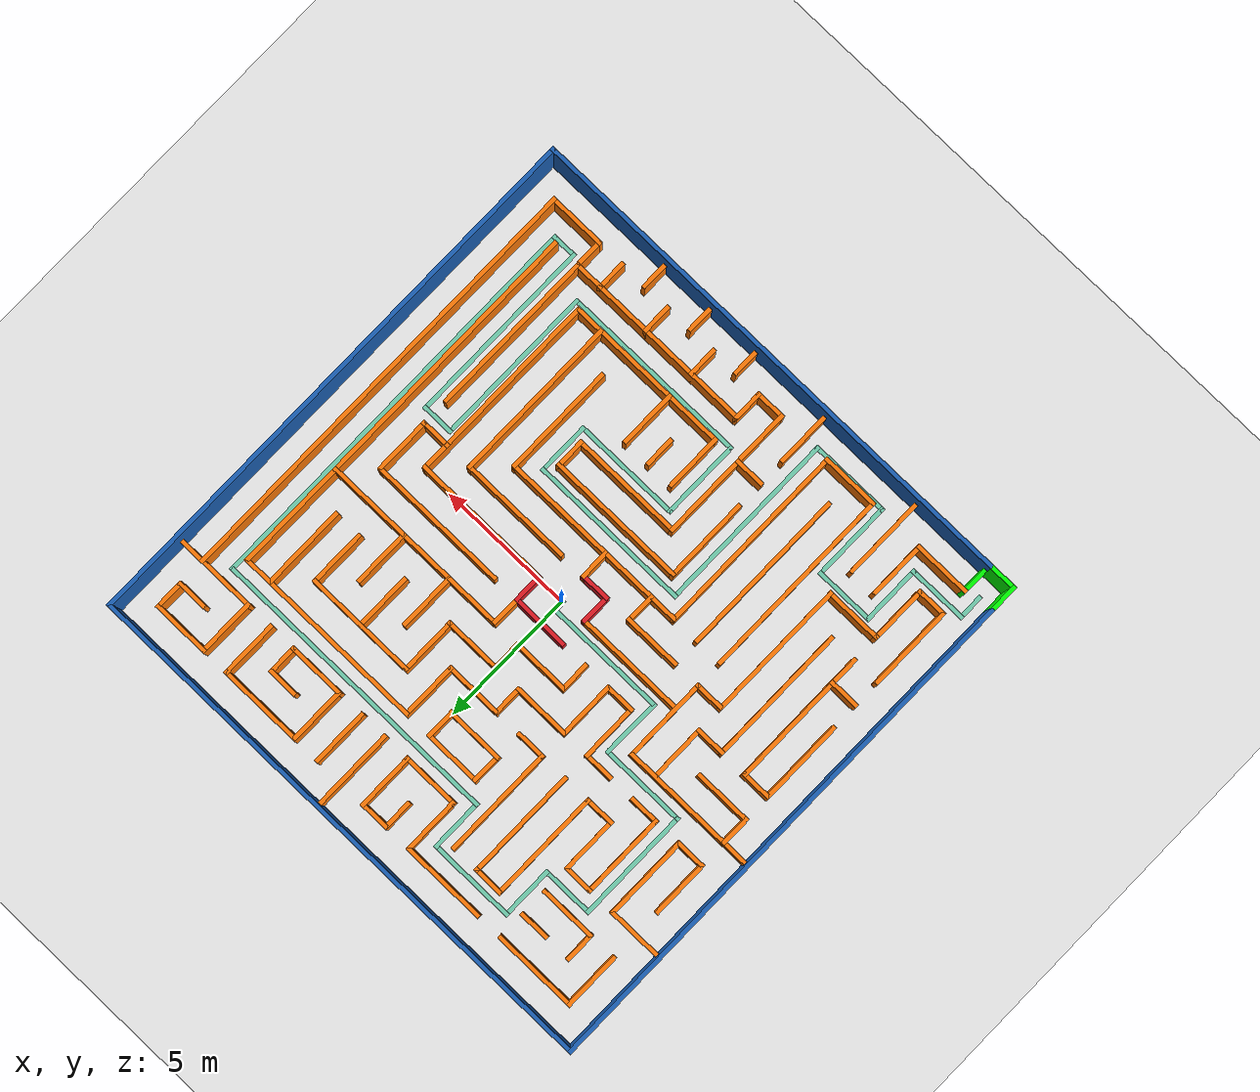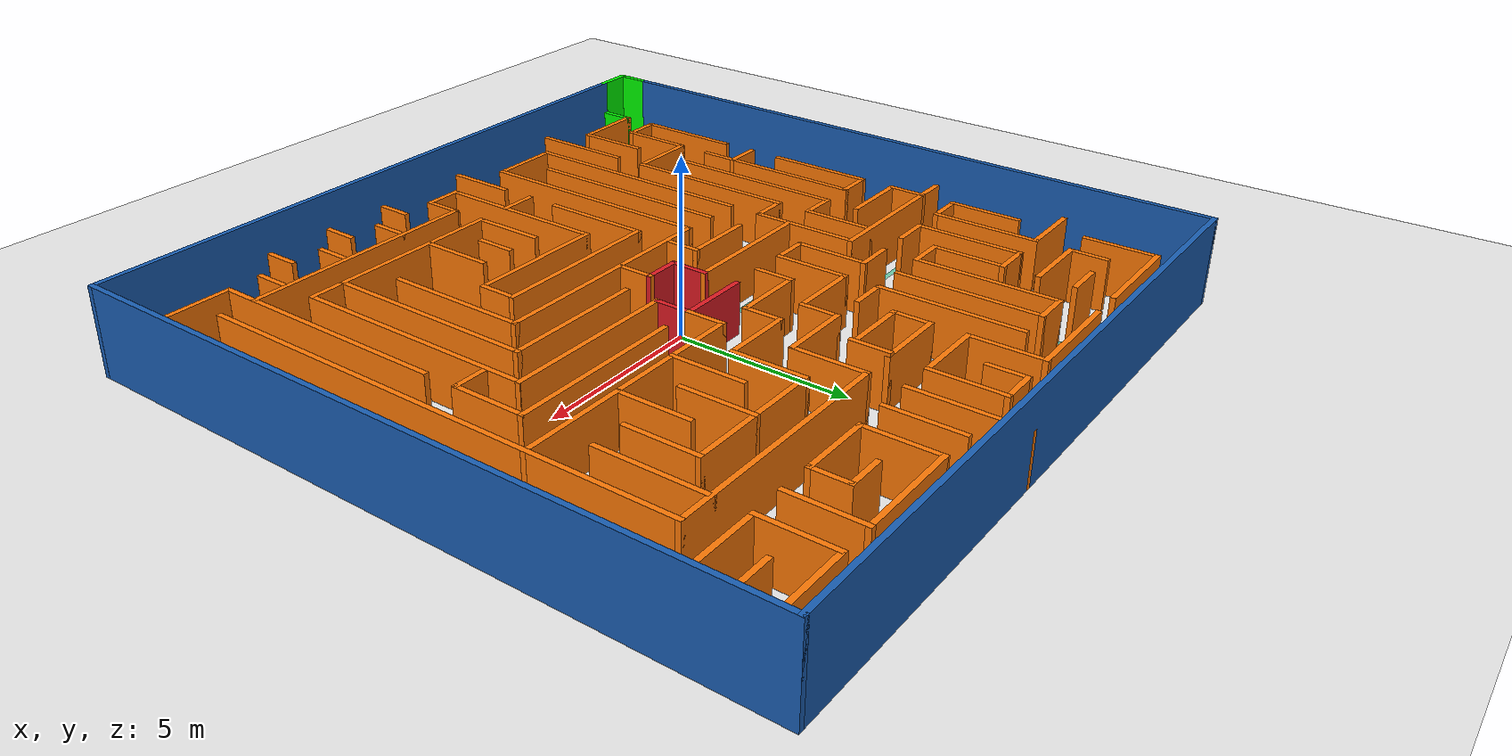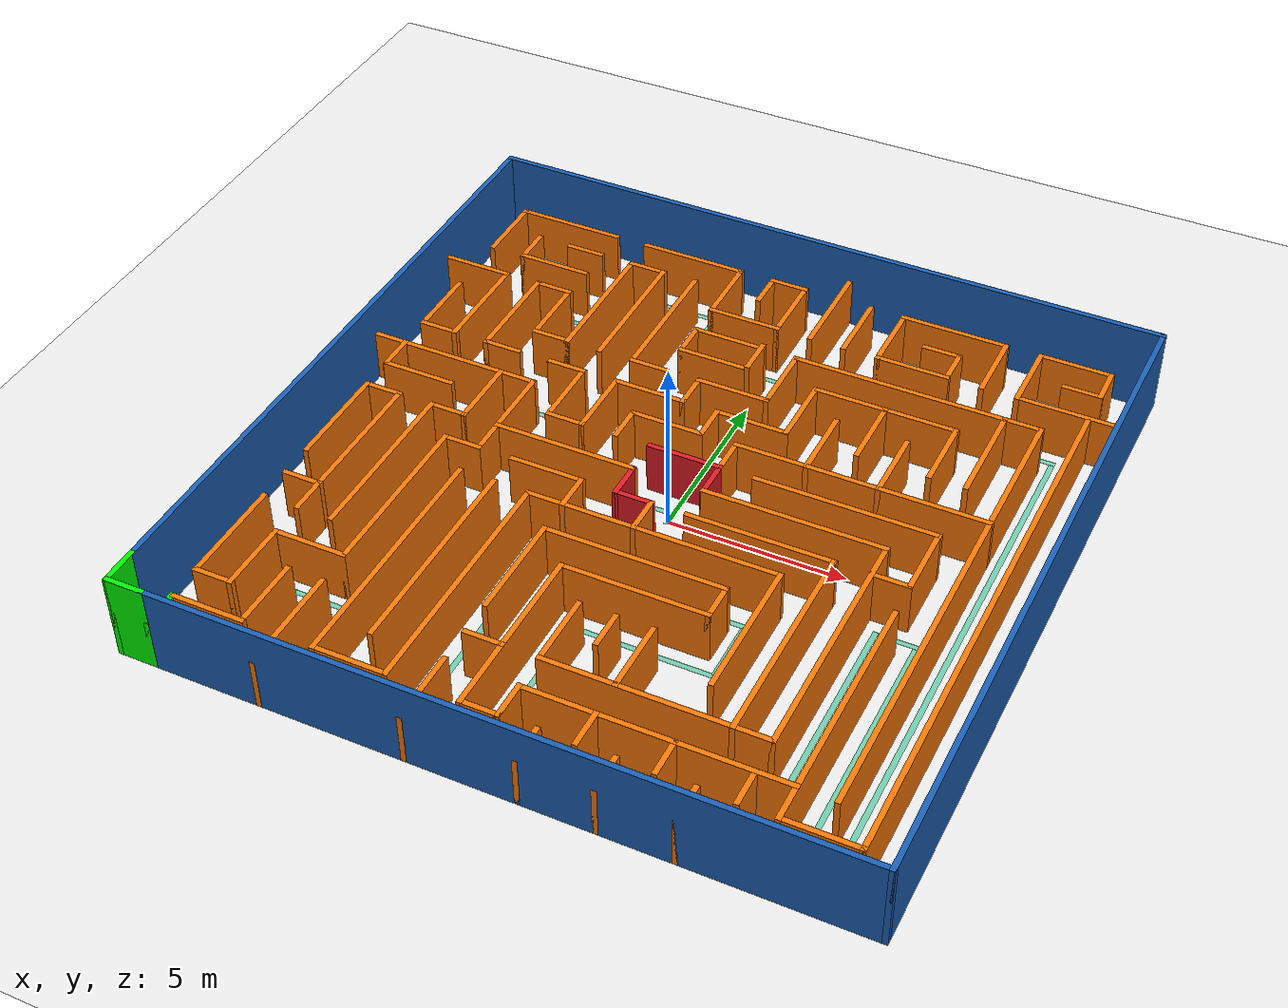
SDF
<sdf version="1.7">
 <world name="default">
  <light name="sun" type="directional">
   <pose>0 0 10 0 -0 0</pose>
   <diffuse>0.8 0.8 0.8 1</diffuse>
   <specular>0.2 0.2 0.2 1</specular>
   <attenuation>
    <range>1000</range>
    <constant>0.9</constant>
    <linear>0.01</linear>
    <quadratic>0.001</quadratic>
   </attenuation>
   <direction>-0.5 0.1 -0.9</direction>
   <spot><inner_angle>0</inner_angle><outer_angle>0</outer_angle><falloff>0</falloff></spot>
  </light>
  <model name="ground_plane">
   <static>1</static>
   <link name="link">
    <collision name="collision">
     <geometry><plane><normal>0 0 1</normal><size>100 100</size></plane></geometry>
     <surface><friction><ode><mu>100</mu><mu2>50</mu2></ode></friction></surface>
    </collision>
    <visual name="visual">
     <cast_shadows>0</cast_shadows>
     <geometry><plane><normal>0 0 1</normal><size>100 100</size></plane></geometry>
     <material>
      <script><uri>file://media/materials/scripts/gazebo.material</uri><name>Gazebo/White</name></script>
     </material>
    </visual>
   </link>
  </model>
  <gravity>0 0 -9.8</gravity>
  <magnetic_field>6e-06 2.3e-05 -4.2e-05</magnetic_field>
  <atmosphere type="adiabatic"/>
  <physics type="ode">
   <max_step_size>0.004</max_step_size>
   <real_time_factor>1</real_time_factor>
   <real_time_update_rate>250</real_time_update_rate>
  </physics>
  <scene><ambient>0.4 0.4 0.4 1</ambient><background>0.7 0.7 0.7 1</background><shadows>1</shadows></scene>
  <audio><device>default</device></audio>
  <spherical_coordinates>
   <surface_model>EARTH_WGS84</surface_model>
   <latitude_deg>0</latitude_deg>
   <longitude_deg>0</longitude_deg>
   <elevation>0</elevation>
   <heading_deg>0</heading_deg>
  </spherical_coordinates>
  <model name="big_maze">
   <link name="Wall_10">
    <collision name="Wall_10_Collision">
     <geometry><box><size>19.15 0.15 2.5</size></box></geometry>
     <pose>0 0 1.25 0 -0 0</pose>
    </collision>
    <visual name="Wall_10_Visual">
     <pose>0 0 1.25 0 -0 0</pose>
     <geometry><box><size>19.15 0.15 2.5</size></box></geometry>
     <material>
      <script><uri>file://media/materials/scripts/gazebo.material</uri><name>Gazebo/Grey</name></script>
      <ambient>0.101961 0.372549 0.705882 1</ambient>
     </material>
     <meta><layer>0</layer></meta>
    </visual>
    <pose>-10 0.5 0 0 -0 1.5708</pose>
   </link>
   <link name="Wall_100">
    <collision name="Wall_100_Collision">
     <geometry><box><size>1.15 0.15 1.6</size></box></geometry>
     <pose>0 0 0.8 0 -0 0</pose>
    </collision>
    <visual name="Wall_100_Visual">
     <pose>0 0 0.8 0 -0 0</pose>
     <geometry><box><size>1.15 0.15 1.6</size></box></geometry>
     <material>
      <script><uri>file://media/materials/scripts/gazebo.material</uri><name>Gazebo/Grey</name></script>
      <ambient>0.996078 0.47451 0.0196078 1</ambient>
     </material>
     <meta><layer>0</layer></meta>
    </visual>
    <pose>0 5.5 0 0 -0 1.5708</pose>
   </link>
   <link name="Wall_102">
    <collision name="Wall_102_Collision">
     <geometry><box><size>2.15 0.15 1.5</size></box></geometry>
     <pose>0 0 0.75 0 -0 0</pose>
    </collision>
    <visual name="Wall_102_Visual">
     <pose>0 0 0.75 0 -0 0</pose>
     <geometry><box><size>2.15 0.15 1.5</size></box></geometry>
     <material>
      <script><uri>file://media/materials/scripts/gazebo.material</uri><name>Gazebo/Grey</name></script>
      <ambient>0.996078 0.47451 0.0196078 1</ambient>
     </material>
     <meta><layer>0</layer></meta>
    </visual>
    <pose>0 8 0 0 -0 1.5708</pose>
   </link>
   <link name="Wall_104">
    <collision name="Wall_104_Collision">
     <geometry><box><size>1.15 0.15 1.5</size></box></geometry>
     <pose>0 0 0.75 0 -0 0</pose>
    </collision>
    <visual name="Wall_104_Visual">
     <pose>0 0 0.75 0 -0 0</pose>
     <geometry><box><size>1.15 0.15 1.5</size></box></geometry>
     <material>
      <script><uri>file://media/materials/scripts/gazebo.material</uri><name>Gazebo/Grey</name></script>
      <ambient>0.996078 0.47451 0.0196078 1</ambient>
     </material>
     <meta><layer>0</layer></meta>
    </visual>
    <pose>1 -9.5 0 0 -0 1.5708</pose>
   </link>
   <link name="Wall_106">
    <collision name="Wall_106_Collision">
     <geometry><box><size>3.15 0.15 1.5</size></box></geometry>
     <pose>0 0 0.75 0 -0 0</pose>
    </collision>
    <visual name="Wall_106_Visual">
     <pose>0 0 0.75 0 -0 0</pose>
     <geometry><box><size>3.15 0.15 1.5</size></box></geometry>
     <material>
      <script><uri>file://media/materials/scripts/gazebo.material</uri><name>Gazebo/Grey</name></script>
      <ambient>0.996078 0.47451 0.0196078 1</ambient>
     </material>
     <meta><layer>0</layer></meta>
    </visual>
    <pose>1 8.5 0 0 -0 1.5708</pose>
   </link>
   <link name="Wall_108">
    <collision name="Wall_108_Collision">
     <geometry><box><size>2.15 0.15 1.5</size></box></geometry>
     <pose>0 0 0.75 0 -0 0</pose>
    </collision>
    <visual name="Wall_108_Visual">
     <pose>0 0 0.75 0 -0 0</pose>
     <geometry><box><size>2.15 0.15 1.5</size></box></geometry>
     <material>
      <script><uri>file://media/materials/scripts/gazebo.material</uri><name>Gazebo/Grey</name></script>
      <ambient>0.996078 0.47451 0.0196078 1</ambient>
     </material>
     <meta><layer>0</layer></meta>
    </visual>
    <pose>1 5 0 0 -0 1.5708</pose>
   </link>
   <link name="Wall_110">
    <collision name="Wall_110_Collision">
     <geometry><box><size>1.15 0.15 1.5</size></box></geometry>
     <pose>0 0 0.75 0 -0 0</pose>
    </collision>
    <visual name="Wall_110_Visual">
     <pose>0 0 0.75 0 -0 0</pose>
     <geometry><box><size>1.15 0.15 1.5</size></box></geometry>
     <material>
      <script><uri>file://media/materials/scripts/gazebo.material</uri><name>Gazebo/Grey</name></script>
      <ambient>0.878431 0.105882 0.141176 1</ambient>
     </material>
     <meta><layer>0</layer></meta>
    </visual>
    <pose>1 0.5 0 0 -0 1.5708</pose>
   </link>
   <link name="Wall_112">
    <collision name="Wall_112_Collision">
     <geometry><box><size>1.15 0.15 1.5</size></box></geometry>
     <pose>0 0 0.75 0 -0 0</pose>
    </collision>
    <visual name="Wall_112_Visual">
     <pose>0 0 0.75 0 -0 0</pose>
     <geometry><box><size>1.15 0.15 1.5</size></box></geometry>
     <material>
      <script><uri>file://media/materials/scripts/gazebo.material</uri><name>Gazebo/Grey</name></script>
      <ambient>0.996078 0.47451 0.0196078 1</ambient>
     </material>
     <meta><layer>0</layer></meta>
    </visual>
    <pose>1 -5.5 0 0 -0 1.5708</pose>
   </link>
   <link name="Wall_114">
    <collision name="Wall_114_Collision">
     <geometry><box><size>1.15 0.15 1.5</size></box></geometry>
     <pose>0 0 0.75 0 -0 0</pose>
    </collision>
    <visual name="Wall_114_Visual">
     <pose>0 0 0.75 0 -0 0</pose>
     <geometry><box><size>1.15 0.15 1.5</size></box></geometry>
     <material>
      <script><uri>file://media/materials/scripts/gazebo.material</uri><name>Gazebo/Grey</name></script>
      <ambient>0.996078 0.47451 0.0196078 1</ambient>
     </material>
     <meta><layer>0</layer></meta>
    </visual>
    <pose>2 -8.5 0 0 -0 1.5708</pose>
   </link>
   <link name="Wall_116">
    <collision name="Wall_116_Collision">
     <geometry><box><size>2.15 0.15 1.5</size></box></geometry>
     <pose>0 0 0.75 0 -0 0</pose>
    </collision>
    <visual name="Wall_116_Visual">
     <pose>0 0 0.75 0 -0 0</pose>
     <geometry><box><size>2.15 0.15 1.5</size></box></geometry>
     <material>
      <script><uri>file://media/materials/scripts/gazebo.material</uri><name>Gazebo/Grey</name></script>
      <ambient>0.996078 0.47451 0.0196078 1</ambient>
     </material>
     <meta><layer>0</layer></meta>
    </visual>
    <pose>2 -6 0 0 -0 1.5708</pose>
   </link>
   <link name="Wall_118">
    <collision name="Wall_118_Collision">
     <geometry><box><size>2.15 0.15 1.5</size></box></geometry>
     <pose>0 0 0.75 0 -0 0</pose>
    </collision>
    <visual name="Wall_118_Visual">
     <pose>0 0 0.75 0 -0 0</pose>
     <geometry><box><size>2.15 0.15 1.5</size></box></geometry>
     <material>
      <script><uri>file://media/materials/scripts/gazebo.material</uri><name>Gazebo/Grey</name></script>
      <ambient>0.996078 0.47451 0.0196078 1</ambient>
     </material>
     <meta><layer>0</layer></meta>
    </visual>
    <pose>2 8 0 0 -0 1.5708</pose>
   </link>
   <link name="Wall_12">
    <collision name="Wall_12_Collision">
     <geometry><box><size>20.15 0.15 2.5</size></box></geometry>
     <pose>0 0 1.25 0 -0 0</pose>
    </collision>
    <visual name="Wall_12_Visual">
     <pose>0 0 1.25 0 -0 0</pose>
     <geometry><box><size>20.15 0.15 2.5</size></box></geometry>
     <material>
      <script><uri>file://media/materials/scripts/gazebo.material</uri><name>Gazebo/Grey</name></script>
      <ambient>0.101961 0.372549 0.705882 1</ambient>
     </material>
     <meta><layer>0</layer></meta>
    </visual>
    <pose>0 10 0 0 -0 0</pose>
   </link>
   <link name="Wall_120">
    <collision name="Wall_120_Collision">
     <geometry><box><size>2.15 0.15 1.5</size></box></geometry>
     <pose>0 0 0.75 0 -0 0</pose>
    </collision>
    <visual name="Wall_120_Visual">
     <pose>0 0 0.75 0 -0 0</pose>
     <geometry><box><size>2.15 0.15 1.5</size></box></geometry>
     <material>
      <script><uri>file://media/materials/scripts/gazebo.material</uri><name>Gazebo/Grey</name></script>
      <ambient>0.996078 0.47451 0.0196078 1</ambient>
     </material>
     <meta><layer>0</layer></meta>
    </visual>
    <pose>2 4 0 0 -0 1.5708</pose>
   </link>
   <link name="Wall_122">
    <collision name="Wall_122_Collision">
     <geometry><box><size>1.15 0.15 1.5</size></box></geometry>
     <pose>0 0 0.75 0 -0 0</pose>
    </collision>
    <visual name="Wall_122_Visual">
     <pose>0 0 0.75 0 -0 0</pose>
     <geometry><box><size>1.15 0.15 1.5</size></box></geometry>
     <material>
      <script><uri>file://media/materials/scripts/gazebo.material</uri><name>Gazebo/Grey</name></script>
      <ambient>0.996078 0.47451 0.0196078 1</ambient>
     </material>
     <meta><layer>0</layer></meta>
    </visual>
    <pose>3 -9.5 0 0 -0 1.5708</pose>
   </link>
   <link name="Wall_124">
    <collision name="Wall_124_Collision">
     <geometry><box><size>2.15 0.15 1.5</size></box></geometry>
     <pose>0 0 0.75 0 -0 0</pose>
    </collision>
    <visual name="Wall_124_Visual">
     <pose>0 0 0.75 0 -0 0</pose>
     <geometry><box><size>2.15 0.15 1.5</size></box></geometry>
     <material>
      <script><uri>file://media/materials/scripts/gazebo.material</uri><name>Gazebo/Grey</name></script>
      <ambient>0.996078 0.47451 0.0196078 1</ambient>
     </material>
     <meta><layer>0</layer></meta>
    </visual>
    <pose>3 8 0 0 -0 1.5708</pose>
   </link>
   <link name="Wall_126">
    <collision name="Wall_126_Collision">
     <geometry><box><size>2.15 0.15 1.5</size></box></geometry>
     <pose>0 0 0.75 0 -0 0</pose>
    </collision>
    <visual name="Wall_126_Visual">
     <pose>0 0 0.75 0 -0 0</pose>
     <geometry><box><size>2.15 0.15 1.5</size></box></geometry>
     <material>
      <script><uri>file://media/materials/scripts/gazebo.material</uri><name>Gazebo/Grey</name></script>
      <ambient>0.996078 0.47451 0.0196078 1</ambient>
     </material>
     <meta><layer>0</layer></meta>
    </visual>
    <pose>3 3 0 0 -0 1.5708</pose>
   </link>
   <link name="Wall_128">
    <collision name="Wall_128_Collision">
     <geometry><box><size>1.15 0.15 1.5</size></box></geometry>
     <pose>0 0 0.75 0 -0 0</pose>
    </collision>
    <visual name="Wall_128_Visual">
     <pose>0 0 0.75 0 -0 0</pose>
     <geometry><box><size>1.15 0.15 1.5</size></box></geometry>
     <material>
      <script><uri>file://media/materials/scripts/gazebo.material</uri><name>Gazebo/Grey</name></script>
      <ambient>0.996078 0.47451 0.0196078 1</ambient>
     </material>
     <meta><layer>0</layer></meta>
    </visual>
    <pose>3 -3.5 0 0 -0 1.5708</pose>
   </link>
   <link name="Wall_130">
    <collision name="Wall_130_Collision">
     <geometry><box><size>2.15 0.15 1.5</size></box></geometry>
     <pose>0 0 0.75 0 -0 0</pose>
    </collision>
    <visual name="Wall_130_Visual">
     <pose>0 0 0.75 0 -0 0</pose>
     <geometry><box><size>2.15 0.15 1.5</size></box></geometry>
     <material>
      <script><uri>file://media/materials/scripts/gazebo.material</uri><name>Gazebo/Grey</name></script>
      <ambient>0.996078 0.47451 0.0196078 1</ambient>
     </material>
     <meta><layer>0</layer></meta>
    </visual>
    <pose>4 4 0 0 -0 1.5708</pose>
   </link>
   <link name="Wall_132">
    <collision name="Wall_132_Collision">
     <geometry><box><size>1.15 0.15 1.5</size></box></geometry>
     <pose>0 0 0.75 0 -0 0</pose>
    </collision>
    <visual name="Wall_132_Visual">
     <pose>0 0 0.75 0 -0 0</pose>
     <geometry><box><size>1.15 0.15 1.5</size></box></geometry>
     <material>
      <script><uri>file://media/materials/scripts/gazebo.material</uri><name>Gazebo/Grey</name></script>
      <ambient>0.996078 0.47451 0.0196078 1</ambient>
     </material>
     <meta><layer>0</layer></meta>
    </visual>
    <pose>4 -8.5 0 0 -0 1.5708</pose>
   </link>
   <link name="Wall_134">
    <collision name="Wall_134_Collision">
     <geometry><box><size>4.15 0.15 1.5</size></box></geometry>
     <pose>0 0 0.75 0 -0 0</pose>
    </collision>
    <visual name="Wall_134_Visual">
     <pose>0 0 0.75 0 -0 0</pose>
     <geometry><box><size>4.15 0.15 1.5</size></box></geometry>
     <material>
      <script><uri>file://media/materials/scripts/gazebo.material</uri><name>Gazebo/Grey</name></script>
      <ambient>0.996078 0.47451 0.0196078 1</ambient>
     </material>
     <meta><layer>0</layer></meta>
    </visual>
    <pose>4 -4 0 0 -0 1.5708</pose>
   </link>
   <link name="Wall_136">
    <collision name="Wall_136_Collision">
     <geometry><box><size>1.15 0.15 1.5</size></box></geometry>
     <pose>0 0 0.75 0 -0 0</pose>
    </collision>
    <visual name="Wall_136_Visual">
     <pose>0 0 0.75 0 -0 0</pose>
     <geometry><box><size>1.15 0.15 1.5</size></box></geometry>
     <material>
      <script><uri>file://media/materials/scripts/gazebo.material</uri><name>Gazebo/Grey</name></script>
      <ambient>0.996078 0.47451 0.0196078 1</ambient>
     </material>
     <meta><layer>0</layer></meta>
    </visual>
    <pose>5 7.5 0 0 -0 -1.5708</pose>
   </link>
   <link name="Wall_138">
    <collision name="Wall_138_Collision">
     <geometry><box><size>2.15 0.15 1.5</size></box></geometry>
     <pose>0 0 0.75 0 -0 0</pose>
    </collision>
    <visual name="Wall_138_Visual">
     <pose>0 0 0.75 0 -0 0</pose>
     <geometry><box><size>2.15 0.15 1.5</size></box></geometry>
     <material>
      <script><uri>file://media/materials/scripts/gazebo.material</uri><name>Gazebo/Grey</name></script>
      <ambient>0.996078 0.47451 0.0196078 1</ambient>
     </material>
     <meta><layer>0</layer></meta>
    </visual>
    <pose>5 3 0 0 -0 1.5708</pose>
   </link>
   <link name="Wall_14">
    <collision name="Wall_14_Collision">
     <geometry><box><size>20.15 0.15 2.5</size></box></geometry>
     <pose>0 0 1.25 0 -0 0</pose>
    </collision>
    <visual name="Wall_14_Visual">
     <pose>0 0 1.25 0 -0 0</pose>
     <geometry><box><size>20.15 0.15 2.5</size></box></geometry>
     <material>
      <script><uri>file://media/materials/scripts/gazebo.material</uri><name>Gazebo/Grey</name></script>
      <ambient>0.101961 0.372549 0.705882 1</ambient>
     </material>
     <meta><layer>0</layer></meta>
    </visual>
    <pose>10 0 0 0 -0 -1.5708</pose>
   </link>
   <link name="Wall_140">
    <collision name="Wall_140_Collision">
     <geometry><box><size>6.15 0.15 1.5</size></box></geometry>
     <pose>0 0 0.75 0 -0 0</pose>
    </collision>
    <visual name="Wall_140_Visual">
     <pose>0 0 0.75 0 -0 0</pose>
     <geometry><box><size>6.15 0.15 1.5</size></box></geometry>
     <material>
      <script><uri>file://media/materials/scripts/gazebo.material</uri><name>Gazebo/Grey</name></script>
      <ambient>0.996078 0.47451 0.0196078 1</ambient>
     </material>
     <meta><layer>0</layer></meta>
    </visual>
    <pose>5 -4 0 0 -0 1.5708</pose>
   </link>
   <link name="Wall_142">
    <collision name="Wall_142_Collision">
     <geometry><box><size>1.15 0.15 1.5</size></box></geometry>
     <pose>0 0 0.75 0 -0 0</pose>
    </collision>
    <visual name="Wall_142_Visual">
     <pose>0 0 0.75 0 -0 0</pose>
     <geometry><box><size>1.15 0.15 1.5</size></box></geometry>
     <material>
      <script><uri>file://media/materials/scripts/gazebo.material</uri><name>Gazebo/Grey</name></script>
      <ambient>0.996078 0.47451 0.0196078 1</ambient>
     </material>
     <meta><layer>0</layer></meta>
    </visual>
    <pose>5 -9.5 0 0 -0 1.5708</pose>
   </link>
   <link name="Wall_144">
    <collision name="Wall_144_Collision">
     <geometry><box><size>2.15 0.15 1.5</size></box></geometry>
     <pose>0 0 0.75 0 -0 0</pose>
    </collision>
    <visual name="Wall_144_Visual">
     <pose>0 0 0.75 0 -0 0</pose>
     <geometry><box><size>2.15 0.15 1.5</size></box></geometry>
     <material>
      <script><uri>file://media/materials/scripts/gazebo.material</uri><name>Gazebo/Grey</name></script>
      <ambient>0.996078 0.47451 0.0196078 1</ambient>
     </material>
     <meta><layer>0</layer></meta>
    </visual>
    <pose>6 8 0 0 -0 1.5708</pose>
   </link>
   <link name="Wall_146">
    <collision name="Wall_146_Collision">
     <geometry><box><size>1.15 0.15 1.5</size></box></geometry>
     <pose>0 0 0.75 0 -0 0</pose>
    </collision>
    <visual name="Wall_146_Visual">
     <pose>0 0 0.75 0 -0 0</pose>
     <geometry><box><size>1.15 0.15 1.5</size></box></geometry>
     <material>
      <script><uri>file://media/materials/scripts/gazebo.material</uri><name>Gazebo/Grey</name></script>
      <ambient>0.996078 0.47451 0.0196078 1</ambient>
     </material>
     <meta><layer>0</layer></meta>
    </visual>
    <pose>6 -8.5 0 0 -0 1.5708</pose>
   </link>
   <link name="Wall_148">
    <collision name="Wall_148_Collision">
     <geometry><box><size>2.15 0.15 1.5</size></box></geometry>
     <pose>0 0 0.75 0 -0 0</pose>
    </collision>
    <visual name="Wall_148_Visual">
     <pose>0 0 0.75 0 -0 0</pose>
     <geometry><box><size>2.15 0.15 1.5</size></box></geometry>
     <material>
      <script><uri>file://media/materials/scripts/gazebo.material</uri><name>Gazebo/Grey</name></script>
      <ambient>0.996078 0.47451 0.0196078 1</ambient>
     </material>
     <meta><layer>0</layer></meta>
    </visual>
    <pose>6 4 0 0 -0 1.5708</pose>
   </link>
   <link name="Wall_150">
    <collision name="Wall_150_Collision">
     <geometry><box><size>7.15 0.15 1.5</size></box></geometry>
     <pose>0 0 0.75 0 -0 0</pose>
    </collision>
    <visual name="Wall_150_Visual">
     <pose>0 0 0.75 0 -0 0</pose>
     <geometry><box><size>7.15 0.15 1.5</size></box></geometry>
     <material>
      <script><uri>file://media/materials/scripts/gazebo.material</uri><name>Gazebo/Grey</name></script>
      <ambient>0.996078 0.47451 0.0196078 1</ambient>
     </material>
     <meta><layer>0</layer></meta>
    </visual>
    <pose>6 -3.5 0 0 -0 1.5708</pose>
   </link>
   <link name="Wall_152">
    <collision name="Wall_152_Collision">
     <geometry><box><size>7.15 0.15 1.5</size></box></geometry>
     <pose>0 0 0.75 0 -0 0</pose>
    </collision>
    <visual name="Wall_152_Visual">
     <pose>0 0 0.75 0 -0 0</pose>
     <geometry><box><size>7.15 0.15 1.5</size></box></geometry>
     <material>
      <script><uri>file://media/materials/scripts/gazebo.material</uri><name>Gazebo/Grey</name></script>
      <ambient>0.996078 0.47451 0.0196078 1</ambient>
     </material>
     <meta><layer>0</layer></meta>
    </visual>
    <pose>7 -5.5 0 0 -0 1.5708</pose>
   </link>
   <link name="Wall_154">
    <collision name="Wall_154_Collision">
     <geometry><box><size>2.15 0.15 1.5</size></box></geometry>
     <pose>0 0 0.75 0 -0 0</pose>
    </collision>
    <visual name="Wall_154_Visual">
     <pose>0 0 0.75 0 -0 0</pose>
     <geometry><box><size>2.15 0.15 1.5</size></box></geometry>
     <material>
      <script><uri>file://media/materials/scripts/gazebo.material</uri><name>Gazebo/Grey</name></script>
      <ambient>0.996078 0.47451 0.0196078 1</ambient>
     </material>
     <meta><layer>0</layer></meta>
    </visual>
    <pose>7 8 0 0 -0 1.5708</pose>
   </link>
   <link name="Wall_156">
    <collision name="Wall_156_Collision">
     <geometry><box><size>3.15 0.15 1.5</size></box></geometry>
     <pose>0 0 0.75 0 -0 0</pose>
    </collision>
    <visual name="Wall_156_Visual">
     <pose>0 0 0.75 0 -0 0</pose>
     <geometry><box><size>3.15 0.15 1.5</size></box></geometry>
     <material>
      <script><uri>file://media/materials/scripts/gazebo.material</uri><name>Gazebo/Grey</name></script>
      <ambient>0.996078 0.47451 0.0196078 1</ambient>
     </material>
     <meta><layer>0</layer></meta>
    </visual>
    <pose>7 4.5 0 0 -0 1.5708</pose>
   </link>
   <link name="Wall_158">
    <collision name="Wall_158_Collision">
     <geometry><box><size>2.15 0.15 1.5</size></box></geometry>
     <pose>0 0 0.75 0 -0 0</pose>
    </collision>
    <visual name="Wall_158_Visual">
     <pose>0 0 0.75 0 -0 0</pose>
     <geometry><box><size>2.15 0.15 1.5</size></box></geometry>
     <material>
      <script><uri>file://media/materials/scripts/gazebo.material</uri><name>Gazebo/Grey</name></script>
      <ambient>0.996078 0.47451 0.0196078 1</ambient>
     </material>
     <meta><layer>0</layer></meta>
    </visual>
    <pose>7 0 0 0 -0 1.5708</pose>
   </link>
   <link name="Wall_16">
    <collision name="Wall_16_Collision">
     <geometry><box><size>1.15 0.15 1.5</size></box></geometry>
     <pose>0 0 0.75 0 -0 0</pose>
    </collision>
    <visual name="Wall_16_Visual">
     <pose>0 0 0.75 0 -0 0</pose>
     <geometry><box><size>1.15 0.15 1.5</size></box></geometry>
     <material>
      <script><uri>file://media/materials/scripts/gazebo.material</uri><name>Gazebo/Grey</name></script>
      <ambient>0 1 0 1</ambient>
     </material>
     <meta><layer>0</layer></meta>
    </visual>
    <pose>-9 -9.5 0 0 -0 1.5708</pose>
   </link>
   <link name="Wall_160">
    <collision name="Wall_160_Collision">
     <geometry><box><size>14.15 0.15 1.5</size></box></geometry>
     <pose>0 0 0.75 0 -0 0</pose>
    </collision>
    <visual name="Wall_160_Visual">
     <pose>0 0 0.75 0 -0 0</pose>
     <geometry><box><size>14.15 0.15 1.5</size></box></geometry>
     <material>
      <script><uri>file://media/materials/scripts/gazebo.material</uri><name>Gazebo/Grey</name></script>
      <ambient>0.996078 0.47451 0.0196078 1</ambient>
     </material>
     <meta><layer>0</layer></meta>
    </visual>
    <pose>8 -1 0 0 -0 1.5708</pose>
   </link>
   <link name="Wall_162">
    <collision name="Wall_162_Collision">
     <geometry><box><size>16.15 0.15 1.5</size></box></geometry>
     <pose>0 0 0.75 0 -0 0</pose>
    </collision>
    <visual name="Wall_162_Visual">
     <pose>0 0 0.75 0 -0 0</pose>
     <geometry><box><size>16.15 0.15 1.5</size></box></geometry>
     <material>
      <script><uri>file://media/materials/scripts/gazebo.material</uri><name>Gazebo/Grey</name></script>
      <ambient>0.996078 0.47451 0.0196078 1</ambient>
     </material>
     <meta><layer>0</layer></meta>
    </visual>
    <pose>9 -1 0 0 -0 1.5708</pose>
   </link>
   <link name="Wall_164">
    <collision name="Wall_164_Collision">
     <geometry><box><size>1.15 0.15 1.5</size></box></geometry>
     <pose>0 0 0.75 0 -0 0</pose>
    </collision>
    <visual name="Wall_164_Visual">
     <pose>0 0 0.75 0 -0 0</pose>
     <geometry><box><size>1.15 0.15 1.5</size></box></geometry>
     <material>
      <script><uri>file://media/materials/scripts/gazebo.material</uri><name>Gazebo/Grey</name></script>
      <ambient>0.996078 0.47451 0.0196078 1</ambient>
     </material>
     <meta><layer>0</layer></meta>
    </visual>
    <pose>9 8.5 0 0 -0 -1.5708</pose>
   </link>
   <link name="Wall_166">
    <collision name="Wall_166_Collision">
     <geometry><box><size>3.15 0.15 1.5</size></box></geometry>
     <pose>0 0 0.75 0 -0 0</pose>
    </collision>
    <visual name="Wall_166_Visual">
     <pose>0 0 0.75 0 -0 0</pose>
     <geometry><box><size>3.15 0.15 1.5</size></box></geometry>
     <material>
      <script><uri>file://media/materials/scripts/gazebo.material</uri><name>Gazebo/Grey</name></script>
      <ambient>0.996078 0.47451 0.0196078 1</ambient>
     </material>
     <meta><layer>0</layer></meta>
    </visual>
    <pose>-7.5 9 0 0 -0 0</pose>
   </link>
   <link name="Wall_168">
    <collision name="Wall_168_Collision">
     <geometry><box><size>3.15 0.15 1.5</size></box></geometry>
     <pose>0 0 0.75 0 -0 0</pose>
    </collision>
    <visual name="Wall_168_Visual">
     <pose>0 0 0.75 0 -0 0</pose>
     <geometry><box><size>3.15 0.15 1.5</size></box></geometry>
     <material>
      <script><uri>file://media/materials/scripts/gazebo.material</uri><name>Gazebo/Grey</name></script>
      <ambient>0.996078 0.47451 0.0196078 1</ambient>
     </material>
     <meta><layer>0</layer></meta>
    </visual>
    <pose>-3.5 9 0 0 -0 0</pose>
   </link>
   <link name="Wall_170">
    <collision name="Wall_170_Collision">
     <geometry><box><size>2.15 0.15 1.5</size></box></geometry>
     <pose>0 0 0.75 0 -0 0</pose>
    </collision>
    <visual name="Wall_170_Visual">
     <pose>0 0 0.75 0 -0 0</pose>
     <geometry><box><size>2.15 0.15 1.5</size></box></geometry>
     <material>
      <script><uri>file://media/materials/scripts/gazebo.material</uri><name>Gazebo/Grey</name></script>
      <ambient>0.996078 0.47451 0.0196078 1</ambient>
     </material>
     <meta><layer>0</layer></meta>
    </visual>
    <pose>8 9 0 0 -0 3.14159</pose>
   </link>
   <link name="Wall_172">
    <collision name="Wall_172_Collision">
     <geometry><box><size>3.15 0.15 1.5</size></box></geometry>
     <pose>0 0 0.75 0 -0 0</pose>
    </collision>
    <visual name="Wall_172_Visual">
     <pose>0 0 0.75 0 -0 0</pose>
     <geometry><box><size>3.15 0.15 1.5</size></box></geometry>
     <material>
      <script><uri>file://media/materials/scripts/gazebo.material</uri><name>Gazebo/Grey</name></script>
      <ambient>0.996078 0.47451 0.0196078 1</ambient>
     </material>
     <meta><layer>0</layer></meta>
    </visual>
    <pose>4.5 9 0 0 -0 0</pose>
   </link>
   <link name="Wall_174">
    <collision name="Wall_174_Collision">
     <geometry><box><size>1.15 0.15 1.5</size></box></geometry>
     <pose>0 0 0.75 0 -0 0</pose>
    </collision>
    <visual name="Wall_174_Visual">
     <pose>0 0 0.75 0 -0 0</pose>
     <geometry><box><size>1.15 0.15 1.5</size></box></geometry>
     <material>
      <script><uri>file://media/materials/scripts/gazebo.material</uri><name>Gazebo/Grey</name></script>
      <ambient>0.996078 0.47451 0.0196078 1</ambient>
     </material>
     <meta><layer>0</layer></meta>
    </visual>
    <pose>-0.5 9 0 0 -0 0</pose>
   </link>
   <link name="Wall_176">
    <collision name="Wall_176_Collision">
     <geometry><box><size>1.15 0.15 1.5</size></box></geometry>
     <pose>0 0 0.75 0 -0 0</pose>
    </collision>
    <visual name="Wall_176_Visual">
     <pose>0 0 0.75 0 -0 0</pose>
     <geometry><box><size>1.15 0.15 1.5</size></box></geometry>
     <material>
      <script><uri>file://media/materials/scripts/gazebo.material</uri><name>Gazebo/Grey</name></script>
      <ambient>0.996078 0.47451 0.0196078 1</ambient>
     </material>
     <meta><layer>0</layer></meta>
    </visual>
    <pose>-6.5 8 0 0 -0 0</pose>
   </link>
   <link name="Wall_178">
    <collision name="Wall_178_Collision">
     <geometry><box><size>1.15 0.15 1.5</size></box></geometry>
     <pose>0 0 0.75 0 -0 0</pose>
    </collision>
    <visual name="Wall_178_Visual">
     <pose>0 0 0.75 0 -0 0</pose>
     <geometry><box><size>1.15 0.15 1.5</size></box></geometry>
     <material>
      <script><uri>file://media/materials/scripts/gazebo.material</uri><name>Gazebo/Grey</name></script>
      <ambient>0.996078 0.47451 0.0196078 1</ambient>
     </material>
     <meta><layer>0</layer></meta>
    </visual>
    <pose>8.5 8 0 0 -0 3.14159</pose>
   </link>
   <link name="Wall_18">
    <collision name="Wall_18_Collision">
     <geometry><box><size>3.15 0.15 1.5</size></box></geometry>
     <pose>0 0 0.75 0 -0 0</pose>
    </collision>
    <visual name="Wall_18_Visual">
     <pose>0 0 0.75 0 -0 0</pose>
     <geometry><box><size>3.15 0.15 1.5</size></box></geometry>
     <material>
      <script><uri>file://media/materials/scripts/gazebo.material</uri><name>Gazebo/Grey</name></script>
      <ambient>0.996078 0.47451 0.0196078 1</ambient>
     </material>
     <meta><layer>0</layer></meta>
    </visual>
    <pose>-9 -6.5 0 0 -0 1.5708</pose>
   </link>
   <link name="Wall_180">
    <collision name="Wall_180_Collision">
     <geometry><box><size>1.15 0.15 1.5</size></box></geometry>
     <pose>0 0 0.75 0 -0 0</pose>
    </collision>
    <visual name="Wall_180_Visual">
     <pose>0 0 0.75 0 -0 0</pose>
     <geometry><box><size>1.15 0.15 1.5</size></box></geometry>
     <material>
      <script><uri>file://media/materials/scripts/gazebo.material</uri><name>Gazebo/Grey</name></script>
      <ambient>0.996078 0.47451 0.0196078 1</ambient>
     </material>
     <meta><layer>0</layer></meta>
    </visual>
    <pose>4.5 8 0 0 -0 0</pose>
   </link>
   <link name="Wall_182">
    <collision name="Wall_182_Collision">
     <geometry><box><size>1.15 0.15 1.5</size></box></geometry>
     <pose>0 0 0.75 0 -0 0</pose>
    </collision>
    <visual name="Wall_182_Visual">
     <pose>0 0 0.75 0 -0 0</pose>
     <geometry><box><size>1.15 0.15 1.5</size></box></geometry>
     <material>
      <script><uri>file://media/materials/scripts/gazebo.material</uri><name>Gazebo/Grey</name></script>
      <ambient>0.996078 0.47451 0.0196078 1</ambient>
     </material>
     <meta><layer>0</layer></meta>
    </visual>
    <pose>-4.5 8 0 0 -0 0</pose>
   </link>
   <link name="Wall_184">
    <collision name="Wall_184_Collision">
     <geometry><box><size>2.15 0.15 1.5</size></box></geometry>
     <pose>0 0 0.75 0 -0 0</pose>
    </collision>
    <visual name="Wall_184_Visual">
     <pose>0 0 0.75 0 -0 0</pose>
     <geometry><box><size>2.15 0.15 1.5</size></box></geometry>
     <material>
      <script><uri>file://media/materials/scripts/gazebo.material</uri><name>Gazebo/Grey</name></script>
      <ambient>0.996078 0.47451 0.0196078 1</ambient>
     </material>
     <meta><layer>0</layer></meta>
    </visual>
    <pose>4 7 0 0 -0 0</pose>
   </link>
   <link name="Wall_186">
    <collision name="Wall_186_Collision">
     <geometry><box><size>2.15 0.15 1.5</size></box></geometry>
     <pose>0 0 0.75 0 -0 0</pose>
    </collision>
    <visual name="Wall_186_Visual">
     <pose>0 0 0.75 0 -0 0</pose>
     <geometry><box><size>2.15 0.15 1.5</size></box></geometry>
     <material>
      <script><uri>file://media/materials/scripts/gazebo.material</uri><name>Gazebo/Grey</name></script>
      <ambient>0.996078 0.47451 0.0196078 1</ambient>
     </material>
     <meta><layer>0</layer></meta>
    </visual>
    <pose>-1 7 0 0 -0 0</pose>
   </link>
   <link name="Wall_188">
    <collision name="Wall_188_Collision">
     <geometry><box><size>3.15 0.15 1.5</size></box></geometry>
     <pose>0 0 0.75 0 -0 0</pose>
    </collision>
    <visual name="Wall_188_Visual">
     <pose>0 0 0.75 0 -0 0</pose>
     <geometry><box><size>3.15 0.15 1.5</size></box></geometry>
     <material>
      <script><uri>file://media/materials/scripts/gazebo.material</uri><name>Gazebo/Grey</name></script>
      <ambient>0.996078 0.47451 0.0196078 1</ambient>
     </material>
     <meta><layer>0</layer></meta>
    </visual>
    <pose>8.5 7 0 0 -0 0</pose>
   </link>
   <link name="Wall_190">
    <collision name="Wall_190_Collision">
     <geometry><box><size>2.15 0.15 1.5</size></box></geometry>
     <pose>0 0 0.75 0 -0 0</pose>
    </collision>
    <visual name="Wall_190_Visual">
     <pose>0 0 0.75 0 -0 0</pose>
     <geometry><box><size>2.15 0.15 1.5</size></box></geometry>
     <material>
      <script><uri>file://media/materials/scripts/gazebo.material</uri><name>Gazebo/Grey</name></script>
      <ambient>0.996078 0.47451 0.0196078 1</ambient>
     </material>
     <meta><layer>0</layer></meta>
    </visual>
    <pose>-7 7 0 0 -0 0</pose>
   </link>
   <link name="Wall_192">
    <collision name="Wall_192_Collision">
     <geometry><box><size>2.15 0.15 1.5</size></box></geometry>
     <pose>0 0 0.75 0 -0 0</pose>
    </collision>
    <visual name="Wall_192_Visual">
     <pose>0 0 0.75 0 -0 0</pose>
     <geometry><box><size>2.15 0.15 1.5</size></box></geometry>
     <material>
      <script><uri>file://media/materials/scripts/gazebo.material</uri><name>Gazebo/Grey</name></script>
      <ambient>0.996078 0.47451 0.0196078 1</ambient>
     </material>
     <meta><layer>0</layer></meta>
    </visual>
    <pose>-9 6 0 0 -0 0</pose>
   </link>
   <link name="Wall_194">
    <collision name="Wall_194_Collision">
     <geometry><box><size>7.15 0.15 1.5</size></box></geometry>
     <pose>0 0 0.75 0 -0 0</pose>
    </collision>
    <visual name="Wall_194_Visual">
     <pose>0 0 0.75 0 -0 0</pose>
     <geometry><box><size>7.15 0.15 1.5</size></box></geometry>
     <material>
      <script><uri>file://media/materials/scripts/gazebo.material</uri><name>Gazebo/Grey</name></script>
      <ambient>0.996078 0.47451 0.0196078 1</ambient>
     </material>
     <meta><layer>0</layer></meta>
    </visual>
    <pose>4.5 6 0 0 -0 0</pose>
   </link>
   <link name="Wall_196">
    <collision name="Wall_196_Collision">
     <geometry><box><size>2.15 0.15 1.5</size></box></geometry>
     <pose>0 0 0.75 0 -0 0</pose>
    </collision>
    <visual name="Wall_196_Visual">
     <pose>0 0 0.75 0 -0 0</pose>
     <geometry><box><size>2.15 0.15 1.5</size></box></geometry>
     <material>
      <script><uri>file://media/materials/scripts/gazebo.material</uri><name>Gazebo/Grey</name></script>
      <ambient>0.996078 0.47451 0.0196078 1</ambient>
     </material>
     <meta><layer>0</layer></meta>
    </visual>
    <pose>-1 6 0 0 -0 0</pose>
   </link>
   <link name="Wall_198">
    <collision name="Wall_198_Collision">
     <geometry><box><size>1.15 0.15 1.5</size></box></geometry>
     <pose>0 0 0.75 0 -0 0</pose>
    </collision>
    <visual name="Wall_198_Visual">
     <pose>0 0 0.75 0 -0 0</pose>
     <geometry><box><size>1.15 0.15 1.5</size></box></geometry>
     <material>
      <script><uri>file://media/materials/scripts/gazebo.material</uri><name>Gazebo/Grey</name></script>
      <ambient>0.996078 0.47451 0.0196078 1</ambient>
     </material>
     <meta><layer>0</layer></meta>
    </visual>
    <pose>-6.5 6 0 0 -0 0</pose>
   </link>
   <link name="Wall_20">
    <collision name="Wall_20_Collision">
     <geometry><box><size>3.15 0.15 1.5</size></box></geometry>
     <pose>0 0 0.75 0 -0 0</pose>
    </collision>
    <visual name="Wall_20_Visual">
     <pose>0 0 0.75 0 -0 0</pose>
     <geometry><box><size>3.15 0.15 1.5</size></box></geometry>
     <material>
      <script><uri>file://media/materials/scripts/gazebo.material</uri><name>Gazebo/Grey</name></script>
      <ambient>0.996078 0.47451 0.0196078 1</ambient>
     </material>
     <meta><layer>0</layer></meta>
    </visual>
    <pose>-9 -1.5 0 0 -0 1.5708</pose>
   </link>
   <link name="Wall_200">
    <collision name="Wall_200_Collision">
     <geometry><box><size>2.15 0.15 1.5</size></box></geometry>
     <pose>0 0 0.75 0 -0 0</pose>
    </collision>
    <visual name="Wall_200_Visual">
     <pose>0 0 0.75 0 -0 0</pose>
     <geometry><box><size>2.15 0.15 1.5</size></box></geometry>
     <material>
      <script><uri>file://media/materials/scripts/gazebo.material</uri><name>Gazebo/Grey</name></script>
      <ambient>0.996078 0.47451 0.0196078 1</ambient>
     </material>
     <meta><layer>0</layer></meta>
    </visual>
    <pose>-1 5 0 0 -0 0</pose>
   </link>
   <link name="Wall_202">
    <collision name="Wall_202_Collision">
     <geometry><box><size>4.15 0.15 1.5</size></box></geometry>
     <pose>0 0 0.75 0 -0 0</pose>
    </collision>
    <visual name="Wall_202_Visual">
     <pose>0 0 0.75 0 -0 0</pose>
     <geometry><box><size>4.15 0.15 1.5</size></box></geometry>
     <material>
      <script><uri>file://media/materials/scripts/gazebo.material</uri><name>Gazebo/Grey</name></script>
      <ambient>0.996078 0.47451 0.0196078 1</ambient>
     </material>
     <meta><layer>0</layer></meta>
    </visual>
    <pose>4 5 0 0 -0 0</pose>
   </link>
   <link name="Wall_204">
    <collision name="Wall_204_Collision">
     <geometry><box><size>1.15 0.15 1.5</size></box></geometry>
     <pose>0 0 0.75 0 -0 0</pose>
    </collision>
    <visual name="Wall_204_Visual">
     <pose>0 0 0.75 0 -0 0</pose>
     <geometry><box><size>1.15 0.15 1.5</size></box></geometry>
     <material>
      <script><uri>file://media/materials/scripts/gazebo.material</uri><name>Gazebo/Grey</name></script>
      <ambient>0.996078 0.47451 0.0196078 1</ambient>
     </material>
     <meta><layer>0</layer></meta>
    </visual>
    <pose>-5.5 4 0 0 -0 0</pose>
   </link>
   <link name="Wall_206">
    <collision name="Wall_206_Collision">
     <geometry><box><size>1.15 0.15 1.5</size></box></geometry>
     <pose>0 0 0.75 0 -0 0</pose>
    </collision>
    <visual name="Wall_206_Visual">
     <pose>0 0 0.75 0 -0 0</pose>
     <geometry><box><size>1.15 0.15 1.5</size></box></geometry>
     <material>
      <script><uri>file://media/materials/scripts/gazebo.material</uri><name>Gazebo/Grey</name></script>
      <ambient>0.996078 0.47451 0.0196078 1</ambient>
     </material>
     <meta><layer>0</layer></meta>
    </visual>
    <pose>-2.5 4 0 0 -0 0</pose>
   </link>
   <link name="Wall_208">
    <collision name="Wall_208_Collision">
     <geometry><box><size>2.15 0.15 1.5</size></box></geometry>
     <pose>0 0 0.75 0 -0 0</pose>
    </collision>
    <visual name="Wall_208_Visual">
     <pose>0 0 0.75 0 -0 0</pose>
     <geometry><box><size>2.15 0.15 1.5</size></box></geometry>
     <material>
      <script><uri>file://media/materials/scripts/gazebo.material</uri><name>Gazebo/Grey</name></script>
      <ambient>0.996078 0.47451 0.0196078 1</ambient>
     </material>
     <meta><layer>0</layer></meta>
    </visual>
    <pose>0 4 0 0 -0 0</pose>
   </link>
   <link name="Wall_210">
    <collision name="Wall_210_Collision">
     <geometry><box><size>1.15 0.15 1.5</size></box></geometry>
     <pose>0 0 0.75 0 -0 0</pose>
    </collision>
    <visual name="Wall_210_Visual">
     <pose>0 0 0.75 0 -0 0</pose>
     <geometry><box><size>1.15 0.15 1.5</size></box></geometry>
     <material>
      <script><uri>file://media/materials/scripts/gazebo.material</uri><name>Gazebo/Grey</name></script>
      <ambient>0.996078 0.47451 0.0196078 1</ambient>
     </material>
     <meta><layer>0</layer></meta>
    </visual>
    <pose>-8.5 3 0 0 -0 0</pose>
   </link>
   <link name="Wall_212">
    <collision name="Wall_212_Collision">
     <geometry><box><size>1.15 0.15 1.5</size></box></geometry>
     <pose>0 0 0.75 0 -0 0</pose>
    </collision>
    <visual name="Wall_212_Visual">
     <pose>0 0 0.75 0 -0 0</pose>
     <geometry><box><size>1.15 0.15 1.5</size></box></geometry>
     <material>
      <script><uri>file://media/materials/scripts/gazebo.material</uri><name>Gazebo/Grey</name></script>
      <ambient>0.996078 0.47451 0.0196078 1</ambient>
     </material>
     <meta><layer>0</layer></meta>
    </visual>
    <pose>-6.5 3 0 0 -0 0</pose>
   </link>
   <link name="Wall_214">
    <collision name="Wall_214_Collision">
     <geometry><box><size>2.15 0.15 1.5</size></box></geometry>
     <pose>0 0 0.75 0 -0 0</pose>
    </collision>
    <visual name="Wall_214_Visual">
     <pose>0 0 0.75 0 -0 0</pose>
     <geometry><box><size>2.15 0.15 1.5</size></box></geometry>
     <material>
      <script><uri>file://media/materials/scripts/gazebo.material</uri><name>Gazebo/Grey</name></script>
      <ambient>0.996078 0.47451 0.0196078 1</ambient>
     </material>
     <meta><layer>0</layer></meta>
    </visual>
    <pose>1 3 0 0 -0 0</pose>
   </link>
   <link name="Wall_216">
    <collision name="Wall_216_Collision">
     <geometry><box><size>2.15 0.15 1.5</size></box></geometry>
     <pose>0 0 0.75 0 -0 0</pose>
    </collision>
    <visual name="Wall_216_Visual">
     <pose>0 0 0.75 0 -0 0</pose>
     <geometry><box><size>2.15 0.15 1.5</size></box></geometry>
     <material>
      <script><uri>file://media/materials/scripts/gazebo.material</uri><name>Gazebo/Grey</name></script>
      <ambient>0.996078 0.47451 0.0196078 1</ambient>
     </material>
     <meta><layer>0</layer></meta>
    </visual>
    <pose>-2 3 0 0 -0 0</pose>
   </link>
   <link name="Wall_218">
    <collision name="Wall_218_Collision">
     <geometry><box><size>1.15 0.15 1.5</size></box></geometry>
     <pose>0 0 0.75 0 -0 0</pose>
    </collision>
    <visual name="Wall_218_Visual">
     <pose>0 0 0.75 0 -0 0</pose>
     <geometry><box><size>1.15 0.15 1.5</size></box></geometry>
     <material>
      <script><uri>file://media/materials/scripts/gazebo.material</uri><name>Gazebo/Grey</name></script>
      <ambient>0.996078 0.47451 0.0196078 1</ambient>
     </material>
     <meta><layer>0</layer></meta>
    </visual>
    <pose>-4.5 3 0 0 -0 0</pose>
   </link>
   <link name="Wall_22">
    <collision name="Wall_22_Collision">
     <geometry><box><size>1.15 0.15 1.5</size></box></geometry>
     <pose>0 0 0.75 0 -0 0</pose>
    </collision>
    <visual name="Wall_22_Visual">
     <pose>0 0 0.75 0 -0 0</pose>
     <geometry><box><size>1.15 0.15 1.5</size></box></geometry>
     <material>
      <script><uri>file://media/materials/scripts/gazebo.material</uri><name>Gazebo/Grey</name></script>
      <ambient>0.996078 0.47451 0.0196078 1</ambient>
     </material>
     <meta><layer>0</layer></meta>
    </visual>
    <pose>-9 1.5 0 0 -0 1.5708</pose>
   </link>
   <link name="Wall_220">
    <collision name="Wall_220_Collision">
     <geometry><box><size>5.15 0.15 1.5</size></box></geometry>
     <pose>0 0 0.75 0 -0 0</pose>
    </collision>
    <visual name="Wall_220_Visual">
     <pose>0 0 0.75 0 -0 0</pose>
     <geometry><box><size>5.15 0.15 1.5</size></box></geometry>
     <material>
      <script><uri>file://media/materials/scripts/gazebo.material</uri><name>Gazebo/Grey</name></script>
      <ambient>0.996078 0.47451 0.0196078 1</ambient>
     </material>
     <meta><layer>0</layer></meta>
    </visual>
    <pose>-7.5 2 0 0 -0 0</pose>
   </link>
   <link name="Wall_222">
    <collision name="Wall_222_Collision">
     <geometry><box><size>2.15 0.15 1.5</size></box></geometry>
     <pose>0 0 0.75 0 -0 0</pose>
    </collision>
    <visual name="Wall_222_Visual">
     <pose>0 0 0.75 0 -0 0</pose>
     <geometry><box><size>2.15 0.15 1.5</size></box></geometry>
     <material>
      <script><uri>file://media/materials/scripts/gazebo.material</uri><name>Gazebo/Grey</name></script>
      <ambient>0.996078 0.47451 0.0196078 1</ambient>
     </material>
     <meta><layer>0</layer></meta>
    </visual>
    <pose>-1 2 0 0 -0 0</pose>
   </link>
   <link name="Wall_224">
    <collision name="Wall_224_Collision">
     <geometry><box><size>7.15 0.15 1.5</size></box></geometry>
     <pose>0 0 0.75 0 -0 0</pose>
    </collision>
    <visual name="Wall_224_Visual">
     <pose>0 0 0.75 0 -0 0</pose>
     <geometry><box><size>7.15 0.15 1.5</size></box></geometry>
     <material>
      <script><uri>file://media/materials/scripts/gazebo.material</uri><name>Gazebo/Grey</name></script>
      <ambient>0.996078 0.47451 0.0196078 1</ambient>
     </material>
     <meta><layer>0</layer></meta>
    </visual>
    <pose>4.5 2 0 0 -0 0</pose>
   </link>
   <link name="Wall_226">
    <collision name="Wall_226_Collision">
     <geometry><box><size>2.15 0.15 1.5</size></box></geometry>
     <pose>0 0 0.75 0 -0 0</pose>
    </collision>
    <visual name="Wall_226_Visual">
     <pose>0 0 0.75 0 -0 0</pose>
     <geometry><box><size>2.15 0.15 1.5</size></box></geometry>
     <material>
      <script><uri>file://media/materials/scripts/gazebo.material</uri><name>Gazebo/Grey</name></script>
      <ambient>0.996078 0.47451 0.0196078 1</ambient>
     </material>
     <meta><layer>0</layer></meta>
    </visual>
    <pose>-8 1 0 0 -0 0</pose>
   </link>
   <link name="Wall_228">
    <collision name="Wall_228_Collision">
     <geometry><box><size>1.15 0.15 1.5</size></box></geometry>
     <pose>0 0 0.75 0 -0 0</pose>
    </collision>
    <visual name="Wall_228_Visual">
     <pose>0 0 0.75 0 -0 0</pose>
     <geometry><box><size>1.15 0.15 1.5</size></box></geometry>
     <material>
      <script><uri>file://media/materials/scripts/gazebo.material</uri><name>Gazebo/Grey</name></script>
      <ambient>0.996078 0.47451 0.0196078 1</ambient>
     </material>
     <meta><layer>0</layer></meta>
    </visual>
    <pose>-3.5 1 0 0 -0 0</pose>
   </link>
   <link name="Wall_230">
    <collision name="Wall_230_Collision">
     <geometry><box><size>5.15 0.15 1.5</size></box></geometry>
     <pose>0 0 0.75 0 -0 0</pose>
    </collision>
    <visual name="Wall_230_Visual">
     <pose>0 0 0.75 0 -0 0</pose>
     <geometry><box><size>5.15 0.15 1.5</size></box></geometry>
     <material>
      <script><uri>file://media/materials/scripts/gazebo.material</uri><name>Gazebo/Grey</name></script>
      <ambient>0.996078 0.47451 0.0196078 1</ambient>
     </material>
     <meta><layer>0</layer></meta>
    </visual>
    <pose>4.5 1 0 0 -0 0</pose>
   </link>
   <link name="Wall_232">
    <collision name="Wall_232_Collision">
     <geometry><box><size>2.15 0.15 1.5</size></box></geometry>
     <pose>0 0 0.75 0 -0 0</pose>
    </collision>
    <visual name="Wall_232_Visual">
     <pose>0 0 0.75 0 -0 0</pose>
     <geometry><box><size>2.15 0.15 1.5</size></box></geometry>
     <material>
      <script><uri>file://media/materials/scripts/gazebo.material</uri><name>Gazebo/Grey</name></script>
      <ambient>0.878431 0.105882 0.141176 1</ambient>
     </material>
     <meta><layer>0</layer></meta>
    </visual>
    <pose>0 1 0 0 -0 0</pose>
   </link>
   <link name="Wall_234">
    <collision name="Wall_234_Collision">
     <geometry><box><size>1.15 0.15 1.5</size></box></geometry>
     <pose>0 0 0.75 0 -0 0</pose>
    </collision>
    <visual name="Wall_234_Visual">
     <pose>0 0 0.75 0 -0 0</pose>
     <geometry><box><size>1.15 0.15 1.5</size></box></geometry>
     <material>
      <script><uri>file://media/materials/scripts/gazebo.material</uri><name>Gazebo/Grey</name></script>
      <ambient>0.996078 0.47451 0.0196078 1</ambient>
     </material>
     <meta><layer>0</layer></meta>
    </visual>
    <pose>-8.5 0 0 0 -0 0</pose>
   </link>
   <link name="Wall_236">
    <collision name="Wall_236_Collision">
     <geometry><box><size>1.15 0.15 1.5</size></box></geometry>
     <pose>0 0 0.75 0 -0 0</pose>
    </collision>
    <visual name="Wall_236_Visual">
     <pose>0 0 0.75 0 -0 0</pose>
     <geometry><box><size>1.15 0.15 1.5</size></box></geometry>
     <material>
      <script><uri>file://media/materials/scripts/gazebo.material</uri><name>Gazebo/Grey</name></script>
      <ambient>0.996078 0.47451 0.0196078 1</ambient>
     </material>
     <meta><layer>0</layer></meta>
    </visual>
    <pose>-6.5 0 0 0 -0 0</pose>
   </link>
   <link name="Wall_238">
    <collision name="Wall_238_Collision">
     <geometry><box><size>4.15 0.15 1.5</size></box></geometry>
     <pose>0 0 0.75 0 -0 0</pose>
    </collision>
    <visual name="Wall_238_Visual">
     <pose>0 0 0.75 0 -0 0</pose>
     <geometry><box><size>4.15 0.15 1.5</size></box></geometry>
     <material>
      <script><uri>file://media/materials/scripts/gazebo.material</uri><name>Gazebo/Grey</name></script>
      <ambient>0.996078 0.47451 0.0196078 1</ambient>
     </material>
     <meta><layer>0</layer></meta>
    </visual>
    <pose>-3 0 0 0 -0 0</pose>
   </link>
   <link name="Wall_24">
    <collision name="Wall_24_Collision">
     <geometry><box><size>2.15 0.15 1.5</size></box></geometry>
     <pose>0 0 0.75 0 -0 0</pose>
    </collision>
    <visual name="Wall_24_Visual">
     <pose>0 0 0.75 0 -0 0</pose>
     <geometry><box><size>2.15 0.15 1.5</size></box></geometry>
     <material>
      <script><uri>file://media/materials/scripts/gazebo.material</uri><name>Gazebo/Grey</name></script>
      <ambient>0.996078 0.47451 0.0196078 1</ambient>
     </material>
     <meta><layer>0</layer></meta>
    </visual>
    <pose>-9 4 0 0 -0 1.5708</pose>
   </link>
   <link name="Wall_240">
    <collision name="Wall_240_Collision">
     <geometry><box><size>5.15 0.15 1.5</size></box></geometry>
     <pose>0 0 0.75 0 -0 0</pose>
    </collision>
    <visual name="Wall_240_Visual">
     <pose>0 0 0.75 0 -0 0</pose>
     <geometry><box><size>5.15 0.15 1.5</size></box></geometry>
     <material>
      <script><uri>file://media/materials/scripts/gazebo.material</uri><name>Gazebo/Grey</name></script>
      <ambient>0.996078 0.47451 0.0196078 1</ambient>
     </material>
     <meta><layer>0</layer></meta>
    </visual>
    <pose>3.5 0 0 0 -0 0</pose>
   </link>
   <link name="Wall_242">
    <collision name="Wall_242_Collision">
     <geometry><box><size>1.15 0.15 1.5</size></box></geometry>
     <pose>0 0 0.75 0 -0 0</pose>
    </collision>
    <visual name="Wall_242_Visual">
     <pose>0 0 0.75 0 -0 0</pose>
     <geometry><box><size>1.15 0.15 1.5</size></box></geometry>
     <material>
      <script><uri>file://media/materials/scripts/gazebo.material</uri><name>Gazebo/Grey</name></script>
      <ambient>0.996078 0.47451 0.0196078 1</ambient>
     </material>
     <meta><layer>0</layer></meta>
    </visual>
    <pose>-5.5 -1 0 0 -0 0</pose>
   </link>
   <link name="Wall_244">
    <collision name="Wall_244_Collision">
     <geometry><box><size>2.15 0.15 1.5</size></box></geometry>
     <pose>0 0 0.75 0 -0 0</pose>
    </collision>
    <visual name="Wall_244_Visual">
     <pose>0 0 0.75 0 -0 0</pose>
     <geometry><box><size>2.15 0.15 1.5</size></box></geometry>
     <material>
      <script><uri>file://media/materials/scripts/gazebo.material</uri><name>Gazebo/Grey</name></script>
      <ambient>0.996078 0.47451 0.0196078 1</ambient>
     </material>
     <meta><layer>0</layer></meta>
    </visual>
    <pose>-3 -1 0 0 -0 0</pose>
   </link>
   <link name="Wall_246">
    <collision name="Wall_246_Collision">
     <geometry><box><size>1.15 0.15 1.5</size></box></geometry>
     <pose>0 0 0.75 0 -0 0</pose>
    </collision>
    <visual name="Wall_246_Visual">
     <pose>0 0 0.75 0 -0 0</pose>
     <geometry><box><size>1.15 0.15 1.5</size></box></geometry>
     <material>
      <script><uri>file://media/materials/scripts/gazebo.material</uri><name>Gazebo/Grey</name></script>
      <ambient>0.996078 0.47451 0.0196078 1</ambient>
     </material>
     <meta><layer>0</layer></meta>
    </visual>
    <pose>6.5 -1 0 0 -0 0</pose>
   </link>
   <link name="Wall_248">
    <collision name="Wall_248_Collision">
     <geometry><box><size>4.15 0.15 1.5</size></box></geometry>
     <pose>0 0 0.75 0 -0 0</pose>
    </collision>
    <visual name="Wall_248_Visual">
     <pose>0 0 0.75 0 -0 0</pose>
     <geometry><box><size>4.15 0.15 1.5</size></box></geometry>
     <material>
      <script><uri>file://media/materials/scripts/gazebo.material</uri><name>Gazebo/Grey</name></script>
      <ambient>0.996078 0.47451 0.0196078 1</ambient>
     </material>
     <meta><layer>0</layer></meta>
    </visual>
    <pose>3 -1 0 0 -0 0</pose>
   </link>
   <link name="Wall_250">
    <collision name="Wall_250_Collision">
     <geometry><box><size>1.15 0.15 1.5</size></box></geometry>
     <pose>0 0 0.75 0 -0 0</pose>
    </collision>
    <visual name="Wall_250_Visual">
     <pose>0 0 0.75 0 -0 0</pose>
     <geometry><box><size>1.15 0.15 1.5</size></box></geometry>
     <material>
      <script><uri>file://media/materials/scripts/gazebo.material</uri><name>Gazebo/Grey</name></script>
      <ambient>0.878431 0.105882 0.141176 1</ambient>
     </material>
     <meta><layer>0</layer></meta>
    </visual>
    <pose>-0.5 -1 0 0 -0 0</pose>
   </link>
   <link name="Wall_252">
    <collision name="Wall_252_Collision">
     <geometry><box><size>7.15 0.15 1.5</size></box></geometry>
     <pose>0 0 0.75 0 -0 0</pose>
    </collision>
    <visual name="Wall_252_Visual">
     <pose>0 0 0.75 0 -0 0</pose>
     <geometry><box><size>7.15 0.15 1.5</size></box></geometry>
     <material>
      <script><uri>file://media/materials/scripts/gazebo.material</uri><name>Gazebo/Grey</name></script>
      <ambient>0.996078 0.47451 0.0196078 1</ambient>
     </material>
     <meta><layer>0</layer></meta>
    </visual>
    <pose>0.5 -2 0 0 -0 0</pose>
   </link>
   <link name="Wall_254">
    <collision name="Wall_254_Collision">
     <geometry><box><size>5.15 0.15 1.5</size></box></geometry>
     <pose>0 0 0.75 0 -0 0</pose>
    </collision>
    <visual name="Wall_254_Visual">
     <pose>0 0 0.75 0 -0 0</pose>
     <geometry><box><size>5.15 0.15 1.5</size></box></geometry>
     <material>
      <script><uri>file://media/materials/scripts/gazebo.material</uri><name>Gazebo/Grey</name></script>
      <ambient>0.996078 0.47451 0.0196078 1</ambient>
     </material>
     <meta><layer>0</layer></meta>
    </visual>
    <pose>0.5 -3 0 0 -0 0</pose>
   </link>
   <link name="Wall_256">
    <collision name="Wall_256_Collision">
     <geometry><box><size>1.15 0.15 1.5</size></box></geometry>
     <pose>0 0 0.75 0 -0 0</pose>
    </collision>
    <visual name="Wall_256_Visual">
     <pose>0 0 0.75 0 -0 0</pose>
     <geometry><box><size>1.15 0.15 1.5</size></box></geometry>
     <material>
      <script><uri>file://media/materials/scripts/gazebo.material</uri><name>Gazebo/Grey</name></script>
      <ambient>0.996078 0.47451 0.0196078 1</ambient>
     </material>
     <meta><layer>0</layer></meta>
    </visual>
    <pose>-8.5 -4 0 0 -0 0</pose>
   </link>
   <link name="Wall_258">
    <collision name="Wall_258_Collision">
     <geometry><box><size>4.15 0.15 1.5</size></box></geometry>
     <pose>0 0 0.75 0 -0 0</pose>
    </collision>
    <visual name="Wall_258_Visual">
     <pose>0 0 0.75 0 -0 0</pose>
     <geometry><box><size>4.15 0.15 1.5</size></box></geometry>
     <material>
      <script><uri>file://media/materials/scripts/gazebo.material</uri><name>Gazebo/Grey</name></script>
      <ambient>0.996078 0.47451 0.0196078 1</ambient>
     </material>
     <meta><layer>0</layer></meta>
    </visual>
    <pose>1 -4 0 0 -0 0</pose>
   </link>
   <link name="Wall_26">
    <collision name="Wall_26_Collision">
     <geometry><box><size>2.15 0.15 1.5</size></box></geometry>
     <pose>0 0 0.75 0 -0 0</pose>
    </collision>
    <visual name="Wall_26_Visual">
     <pose>0 0 0.75 0 -0 0</pose>
     <geometry><box><size>2.15 0.15 1.5</size></box></geometry>
     <material>
      <script><uri>file://media/materials/scripts/gazebo.material</uri><name>Gazebo/Grey</name></script>
      <ambient>0.996078 0.47451 0.0196078 1</ambient>
     </material>
     <meta><layer>0</layer></meta>
    </visual>
    <pose>-9 8 0 0 -0 1.5708</pose>
   </link>
   <link name="Wall_260">
    <collision name="Wall_260_Collision">
     <geometry><box><size>2.15 0.15 1.5</size></box></geometry>
     <pose>0 0 0.75 0 -0 0</pose>
    </collision>
    <visual name="Wall_260_Visual">
     <pose>0 0 0.75 0 -0 0</pose>
     <geometry><box><size>2.15 0.15 1.5</size></box></geometry>
     <material>
      <script><uri>file://media/materials/scripts/gazebo.material</uri><name>Gazebo/Grey</name></script>
      <ambient>0.996078 0.47451 0.0196078 1</ambient>
     </material>
     <meta><layer>0</layer></meta>
    </visual>
    <pose>-7 -6 0 0 -0 0</pose>
   </link>
   <link name="Wall_262">
    <collision name="Wall_262_Collision">
     <geometry><box><size>6.15 0.15 1.5</size></box></geometry>
     <pose>0 0 0.75 0 -0 0</pose>
    </collision>
    <visual name="Wall_262_Visual">
     <pose>0 0 0.75 0 -0 0</pose>
     <geometry><box><size>6.15 0.15 1.5</size></box></geometry>
     <material>
      <script><uri>file://media/materials/scripts/gazebo.material</uri><name>Gazebo/Grey</name></script>
      <ambient>0.996078 0.47451 0.0196078 1</ambient>
     </material>
     <meta><layer>0</layer></meta>
    </visual>
    <pose>3 -7 0 0 -0 0</pose>
   </link>
   <link name="Wall_265">
    <collision name="Wall_265_Collision">
     <geometry><box><size>1.15 0.15 1.5</size></box></geometry>
     <pose>0 0 0.75 0 -0 0</pose>
    </collision>
    <visual name="Wall_265_Visual">
     <pose>0 0 0.75 0 -0 0</pose>
     <geometry><box><size>1.15 0.15 1.5</size></box></geometry>
     <material>
      <script><uri>file://media/materials/scripts/gazebo.material</uri><name>Gazebo/Grey</name></script>
      <ambient>0.996078 0.47451 0.0196078 1</ambient>
     </material>
     <meta><layer>0</layer></meta>
    </visual>
    <pose>-1.5 -7 0 0 -0 0</pose>
   </link>
   <link name="Wall_267">
    <collision name="Wall_267_Collision">
     <geometry><box><size>1.15 0.15 1.5</size></box></geometry>
     <pose>0 0 0.75 0 -0 0</pose>
    </collision>
    <visual name="Wall_267_Visual">
     <pose>0 0 0.75 0 -0 0</pose>
     <geometry><box><size>1.15 0.15 1.5</size></box></geometry>
     <material>
      <script><uri>file://media/materials/scripts/gazebo.material</uri><name>Gazebo/Grey</name></script>
      <ambient>0.996078 0.47451 0.0196078 1</ambient>
     </material>
     <meta><layer>0</layer></meta>
    </visual>
    <pose>-8.5 -8 0 0 -0 0</pose>
   </link>
   <link name="Wall_269">
    <collision name="Wall_269_Collision">
     <geometry><box><size>7.15 0.15 1.5</size></box></geometry>
     <pose>0 0 0.75 0 -0 0</pose>
    </collision>
    <visual name="Wall_269_Visual">
     <pose>0 0 0.75 0 -0 0</pose>
     <geometry><box><size>7.15 0.15 1.5</size></box></geometry>
     <material>
      <script><uri>file://media/materials/scripts/gazebo.material</uri><name>Gazebo/Grey</name></script>
      <ambient>0.996078 0.47451 0.0196078 1</ambient>
     </material>
     <meta><layer>0</layer></meta>
    </visual>
    <pose>3.5 -8 0 0 -0 0</pose>
   </link>
   <link name="Wall_271">
    <collision name="Wall_271_Collision">
     <geometry><box><size>2.15 0.15 1.5</size></box></geometry>
     <pose>0 0 0.75 0 -0 0</pose>
    </collision>
    <visual name="Wall_271_Visual">
     <pose>0 0 0.75 0 -0 0</pose>
     <geometry><box><size>2.15 0.15 1.5</size></box></geometry>
     <material>
      <script><uri>file://media/materials/scripts/gazebo.material</uri><name>Gazebo/Grey</name></script>
      <ambient>0.996078 0.47451 0.0196078 1</ambient>
     </material>
     <meta><layer>0</layer></meta>
    </visual>
    <pose>-8 -9 0 0 -0 0</pose>
   </link>
   <link name="Wall_273">
    <collision name="Wall_273_Collision">
     <geometry><box><size>2.15 0.15 1.5</size></box></geometry>
     <pose>0 0 0.75 0 -0 0</pose>
    </collision>
    <visual name="Wall_273_Visual">
     <pose>0 0 0.75 0 -0 0</pose>
     <geometry><box><size>2.15 0.15 1.5</size></box></geometry>
     <material>
      <script><uri>file://media/materials/scripts/gazebo.material</uri><name>Gazebo/Grey</name></script>
      <ambient>0.996078 0.47451 0.0196078 1</ambient>
     </material>
     <meta><layer>0</layer></meta>
    </visual>
    <pose>8 -9 0 0 -0 0</pose>
   </link>
   <link name="Wall_275">
    <collision name="Wall_275_Collision">
     <geometry><box><size>1.15 0.15 1.5</size></box></geometry>
     <pose>0 0 0.75 0 -0 0</pose>
    </collision>
    <visual name="Wall_275_Visual">
     <pose>0 0 0.75 0 -0 0</pose>
     <geometry><box><size>1.15 0.15 1.5</size></box></geometry>
     <material>
      <script><uri>file://media/materials/scripts/gazebo.material</uri><name>Gazebo/Grey</name></script>
      <ambient>0.996078 0.47451 0.0196078 1</ambient>
     </material>
     <meta><layer>0</layer></meta>
    </visual>
    <pose>-0.5 -9 0 0 -0 0</pose>
   </link>
   <link name="Wall_277">
    <collision name="Wall_277_Collision">
     <geometry><box><size>2.15 0.15 1.5</size></box></geometry>
     <pose>0 0 0.75 0 -0 0</pose>
    </collision>
    <visual name="Wall_277_Visual">
     <pose>0 0 0.75 0 -0 0</pose>
     <geometry><box><size>2.15 0.15 1.5</size></box></geometry>
     <material>
      <script><uri>file://media/materials/scripts/gazebo.material</uri><name>Gazebo/Grey</name></script>
      <ambient>0.996078 0.47451 0.0196078 1</ambient>
     </material>
     <meta><layer>0</layer></meta>
    </visual>
    <pose>-4 -9 0 0 -0 0</pose>
   </link>
   <link name="Wall_28">
    <collision name="Wall_28_Collision">
     <geometry><box><size>1.15 0.15 1.5</size></box></geometry>
     <pose>0 0 0.75 0 -0 0</pose>
    </collision>
    <visual name="Wall_28_Visual">
     <pose>0 0 0.75 0 -0 0</pose>
     <geometry><box><size>1.15 0.15 1.5</size></box></geometry>
     <material>
      <script><uri>file://media/materials/scripts/gazebo.material</uri><name>Gazebo/Grey</name></script>
      <ambient>0.996078 0.47451 0.0196078 1</ambient>
     </material>
     <meta><layer>0</layer></meta>
    </visual>
    <pose>-8 7.5 0 0 -0 -1.5708</pose>
   </link>
   <link name="Wall_282">
    <collision name="Wall_282_Collision"><geometry><box><size>0.500944 0.15 0</size></box></geometry></collision>
    <visual name="Wall_282_Visual">
     <geometry><box><size>0.500944 0.15 0</size></box></geometry>
     <material>
      <script><uri>file://media/materials/scripts/gazebo.material</uri><name>Gazebo/Grey</name></script>
      <ambient>0.435294 0.796078 0.67451 1</ambient>
     </material>
     <meta><layer>0</layer></meta>
    </visual>
    <pose>-0.041 0.151 0 0 -0 1.6563</pose>
   </link>
   <link name="Wall_283">
    <collision name="Wall_283_Collision"><geometry><box><size>4.5002 0.15 0</size></box></geometry></collision>
    <visual name="Wall_283_Visual">
     <geometry><box><size>4.5002 0.15 0</size></box></geometry>
     <material>
      <script><uri>file://media/materials/scripts/gazebo.material</uri><name>Gazebo/Grey</name></script>
      <ambient>0.435294 0.796078 0.67451 1</ambient>
     </material>
     <meta><layer>0</layer></meta>
    </visual>
    <pose>-2.2315 0.326 0 0 -0 3.14159</pose>
   </link>
   <link name="Wall_284">
    <collision name="Wall_284_Collision"><geometry><box><size>2.25 0.15 0</size></box></geometry></collision>
    <visual name="Wall_284_Visual">
     <geometry><box><size>2.25 0.15 0</size></box></geometry>
     <material>
      <script><uri>file://media/materials/scripts/gazebo.material</uri><name>Gazebo/Grey</name></script>
      <ambient>0.435294 0.796078 0.67451 1</ambient>
     </material>
     <meta><layer>0</layer></meta>
    </visual>
    <pose>-4.3915 1.376 0 0 -0 1.55604</pose>
   </link>
   <link name="Wall_288">
    <collision name="Wall_288_Collision"><geometry><box><size>3.2192 0.15 0</size></box></geometry></collision>
    <visual name="Wall_288_Visual">
     <geometry><box><size>3.2192 0.15 0</size></box></geometry>
     <material>
      <script><uri>file://media/materials/scripts/gazebo.material</uri><name>Gazebo/Grey</name></script>
      <ambient>0.435294 0.796078 0.67451 1</ambient>
     </material>
     <meta><layer>0</layer></meta>
    </visual>
    <pose>-5.9105 2.426 0 0 -0 3.14159</pose>
   </link>
   <link name="Wall_289">
    <collision name="Wall_289_Collision"><geometry><box><size>4.25 0.15 0</size></box></geometry></collision>
    <visual name="Wall_289_Visual">
     <geometry><box><size>4.25 0.15 0</size></box></geometry>
     <material>
      <script><uri>file://media/materials/scripts/gazebo.material</uri><name>Gazebo/Grey</name></script>
      <ambient>0.435294 0.796078 0.67451 1</ambient>
     </material>
     <meta><layer>0</layer></meta>
    </visual>
    <pose>-7.445 4.476 0 0 -0 1.5708</pose>
   </link>
   <link name="Wall_290">
    <collision name="Wall_290_Collision"><geometry><box><size>1.969 0.15 0</size></box></geometry></collision>
    <visual name="Wall_290_Visual">
     <geometry><box><size>1.969 0.15 0</size></box></geometry>
     <material>
      <script><uri>file://media/materials/scripts/gazebo.material</uri><name>Gazebo/Grey</name></script>
      <ambient>0.435294 0.796078 0.67451 1</ambient>
     </material>
     <meta><layer>0</layer></meta>
    </visual>
    <pose>-6.5355 6.526 0 0 -0 0</pose>
   </link>
   <link name="Wall_294">
    <collision name="Wall_294_Collision"><geometry><box><size>2 0.15 0</size></box></geometry></collision>
    <visual name="Wall_294_Visual">
     <geometry><box><size>2 0.15 0</size></box></geometry>
     <material>
      <script><uri>file://media/materials/scripts/gazebo.material</uri><name>Gazebo/Grey</name></script>
      <ambient>0.435294 0.796078 0.67451 1</ambient>
     </material>
     <meta><layer>0</layer></meta>
    </visual>
    <pose>-5.626 7.451 0 0 -0 1.5708</pose>
   </link>
   <link name="Wall_295">
    <collision name="Wall_295_Collision"><geometry><box><size>3.25 0.15 0</size></box></geometry></collision>
    <visual name="Wall_295_Visual">
     <geometry><box><size>3.25 0.15 0</size></box></geometry>
     <material>
      <script><uri>file://media/materials/scripts/gazebo.material</uri><name>Gazebo/Grey</name></script>
      <ambient>0.435294 0.796078 0.67451 1</ambient>
     </material>
     <meta><layer>0</layer></meta>
    </visual>
    <pose>-4.076 8.376 0 0 -0 0</pose>
   </link>
   <link name="Wall_296">
    <collision name="Wall_296_Collision"><geometry><box><size>2 0.15 0</size></box></geometry></collision>
    <visual name="Wall_296_Visual">
     <geometry><box><size>2 0.15 0</size></box></geometry>
     <material>
      <script><uri>file://media/materials/scripts/gazebo.material</uri><name>Gazebo/Grey</name></script>
      <ambient>0.435294 0.796078 0.67451 1</ambient>
     </material>
     <meta><layer>0</layer></meta>
    </visual>
    <pose>-2.526 7.451 0 0 -0 -1.5708</pose>
   </link>
   <link name="Wall_297">
    <collision name="Wall_297_Collision"><geometry><box><size>11 0.15 0</size></box></geometry></collision>
    <visual name="Wall_297_Visual">
     <geometry><box><size>11 0.15 0</size></box></geometry>
     <material>
      <script><uri>file://media/materials/scripts/gazebo.material</uri><name>Gazebo/Grey</name></script>
      <ambient>0.435294 0.796078 0.67451 1</ambient>
     </material>
     <meta><layer>0</layer></meta>
    </visual>
    <pose>2.899 6.526 0 0 -0 0</pose>
   </link>
   <link name="Wall_298">
    <collision name="Wall_298_Collision"><geometry><box><size>15 0.15 0</size></box></geometry></collision>
    <visual name="Wall_298_Visual">
     <geometry><box><size>15 0.15 0</size></box></geometry>
     <material>
      <script><uri>file://media/materials/scripts/gazebo.material</uri><name>Gazebo/Grey</name></script>
      <ambient>0.435294 0.796078 0.67451 1</ambient>
     </material>
     <meta><layer>0</layer></meta>
    </visual>
    <pose>8.324 -0.899 0 0 -0 -1.5708</pose>
   </link>
   <link name="Wall_299">
    <collision name="Wall_299_Collision"><geometry><box><size>1 0.15 0</size></box></geometry></collision>
    <visual name="Wall_299_Visual">
     <geometry><box><size>1 0.15 0</size></box></geometry>
     <material>
      <script><uri>file://media/materials/scripts/gazebo.material</uri><name>Gazebo/Grey</name></script>
      <ambient>0.435294 0.796078 0.67451 1</ambient>
     </material>
     <meta><layer>0</layer></meta>
    </visual>
    <pose>7.899 -8.324 0 0 -0 3.14159</pose>
   </link>
   <link name="Wall_30">
    <collision name="Wall_30_Collision">
     <geometry><box><size>3.15 0.15 1.5</size></box></geometry>
     <pose>0 0 0.75 0 -0 0</pose>
    </collision>
    <visual name="Wall_30_Visual">
     <pose>0 0 0.75 0 -0 0</pose>
     <geometry><box><size>3.15 0.15 1.5</size></box></geometry>
     <material>
      <script><uri>file://media/materials/scripts/gazebo.material</uri><name>Gazebo/Grey</name></script>
      <ambient>0.996078 0.47451 0.0196078 1</ambient>
     </material>
     <meta><layer>0</layer></meta>
    </visual>
    <pose>-8 4.5 0 0 -0 -1.5708</pose>
   </link>
   <link name="Wall_300">
    <collision name="Wall_300_Collision"><geometry><box><size>7 0.15 0</size></box></geometry></collision>
    <visual name="Wall_300_Visual">
     <geometry><box><size>7 0.15 0</size></box></geometry>
     <material>
      <script><uri>file://media/materials/scripts/gazebo.material</uri><name>Gazebo/Grey</name></script>
      <ambient>0.435294 0.796078 0.67451 1</ambient>
     </material>
     <meta><layer>0</layer></meta>
    </visual>
    <pose>7.474 -4.899 0 0 -0 1.5708</pose>
   </link>
   <link name="Wall_301">
    <collision name="Wall_301_Collision"><geometry><box><size>1.25 0.15 0</size></box></geometry></collision>
    <visual name="Wall_301_Visual">
     <geometry><box><size>1.25 0.15 0</size></box></geometry>
     <material>
      <script><uri>file://media/materials/scripts/gazebo.material</uri><name>Gazebo/Grey</name></script>
      <ambient>0.435294 0.796078 0.67451 1</ambient>
     </material>
     <meta><layer>0</layer></meta>
    </visual>
    <pose>6.924 -1.474 0 0 -0 3.14159</pose>
   </link>
   <link name="Wall_302">
    <collision name="Wall_302_Collision"><geometry><box><size>6 0.15 0</size></box></geometry></collision>
    <visual name="Wall_302_Visual">
     <geometry><box><size>6 0.15 0</size></box></geometry>
     <material>
      <script><uri>file://media/materials/scripts/gazebo.material</uri><name>Gazebo/Grey</name></script>
      <ambient>0.435294 0.796078 0.67451 1</ambient>
     </material>
     <meta><layer>0</layer></meta>
    </visual>
    <pose>6.374 -4.399 0 0 -0 -1.5708</pose>
   </link>
   <link name="Wall_303">
    <collision name="Wall_303_Collision"><geometry><box><size>7 0.15 0</size></box></geometry></collision>
    <visual name="Wall_303_Visual">
     <geometry><box><size>7 0.15 0</size></box></geometry>
     <material>
      <script><uri>file://media/materials/scripts/gazebo.material</uri><name>Gazebo/Grey</name></script>
      <ambient>0.435294 0.796078 0.67451 1</ambient>
     </material>
     <meta><layer>0</layer></meta>
    </visual>
    <pose>2.949 -7.324 0 0 -0 3.14159</pose>
   </link>
   <link name="Wall_304">
    <collision name="Wall_304_Collision"><geometry><box><size>2.974 0.15 0</size></box></geometry></collision>
    <visual name="Wall_304_Visual">
     <geometry><box><size>2.974 0.15 0</size></box></geometry>
     <material>
      <script><uri>file://media/materials/scripts/gazebo.material</uri><name>Gazebo/Grey</name></script>
      <ambient>0.435294 0.796078 0.67451 1</ambient>
     </material>
     <meta><layer>0</layer></meta>
    </visual>
    <pose>-0.476 -5.912 0 0 -0 1.5708</pose>
   </link>
   <link name="Wall_306">
    <collision name="Wall_306_Collision"><geometry><box><size>4 0.15 0</size></box></geometry></collision>
    <visual name="Wall_306_Visual">
     <geometry><box><size>4 0.15 0</size></box></geometry>
     <material>
      <script><uri>file://media/materials/scripts/gazebo.material</uri><name>Gazebo/Grey</name></script>
      <ambient>0.435294 0.796078 0.67451 1</ambient>
     </material>
     <meta><layer>0</layer></meta>
    </visual>
    <pose>1.449 -4.5 0 0 -0 0</pose>
   </link>
   <link name="Wall_307">
    <collision name="Wall_307_Collision"><geometry><box><size>2 0.15 0</size></box></geometry></collision>
    <visual name="Wall_307_Visual">
     <geometry><box><size>2 0.15 0</size></box></geometry>
     <material>
      <script><uri>file://media/materials/scripts/gazebo.material</uri><name>Gazebo/Grey</name></script>
      <ambient>0.435294 0.796078 0.67451 1</ambient>
     </material>
     <meta><layer>0</layer></meta>
    </visual>
    <pose>3.374 -3.575 0 0 -0 1.5708</pose>
   </link>
   <link name="Wall_308">
    <collision name="Wall_308_Collision"><geometry><box><size>6 0.15 0</size></box></geometry></collision>
    <visual name="Wall_308_Visual">
     <geometry><box><size>6 0.15 0</size></box></geometry>
     <material>
      <script><uri>file://media/materials/scripts/gazebo.material</uri><name>Gazebo/Grey</name></script>
      <ambient>0.435294 0.796078 0.67451 1</ambient>
     </material>
     <meta><layer>0</layer></meta>
    </visual>
    <pose>0.449 -2.65 0 0 -0 3.14159</pose>
   </link>
   <link name="Wall_309">
    <collision name="Wall_309_Collision"><geometry><box><size>6.75 0.15 0</size></box></geometry></collision>
    <visual name="Wall_309_Visual">
     <geometry><box><size>6.75 0.15 0</size></box></geometry>
     <material>
      <script><uri>file://media/materials/scripts/gazebo.material</uri><name>Gazebo/Grey</name></script>
      <ambient>0.435294 0.796078 0.67451 1</ambient>
     </material>
     <meta><layer>0</layer></meta>
    </visual>
    <pose>-2.476 -5.95 0 0 -0 -1.5708</pose>
   </link>
   <link name="Wall_310">
    <collision name="Wall_310_Collision"><geometry><box><size>3 0.15 0</size></box></geometry></collision>
    <visual name="Wall_310_Visual">
     <geometry><box><size>3 0.15 0</size></box></geometry>
     <material>
      <script><uri>file://media/materials/scripts/gazebo.material</uri><name>Gazebo/Grey</name></script>
      <ambient>0.435294 0.796078 0.67451 1</ambient>
     </material>
     <meta><layer>0</layer></meta>
    </visual>
    <pose>-3.901 -9.25 0 0 -0 3.14159</pose>
   </link>
   <link name="Wall_311">
    <collision name="Wall_311_Collision"><geometry><box><size>3.00016 0.15 0</size></box></geometry></collision>
    <visual name="Wall_311_Visual">
     <geometry><box><size>3.00016 0.15 0</size></box></geometry>
     <material>
      <script><uri>file://media/materials/scripts/gazebo.material</uri><name>Gazebo/Grey</name></script>
      <ambient>0.435294 0.796078 0.67451 1</ambient>
     </material>
     <meta><layer>0</layer></meta>
    </visual>
    <pose>-5.326 -7.825 0 0 -0 1.5708</pose>
   </link>
   <link name="Wall_312">
    <collision name="Wall_312_Collision"><geometry><box><size>2.25 0.15 0</size></box></geometry></collision>
    <visual name="Wall_312_Visual">
     <geometry><box><size>2.25 0.15 0</size></box></geometry>
     <material>
      <script><uri>file://media/materials/scripts/gazebo.material</uri><name>Gazebo/Grey</name></script>
      <ambient>0.435294 0.796078 0.67451 1</ambient>
     </material>
     <meta><layer>0</layer></meta>
    </visual>
    <pose>-6.376 -6.4 0 0 -0 3.14159</pose>
   </link>
   <link name="Wall_313">
    <collision name="Wall_313_Collision"><geometry><box><size>2.25022 0.15 0</size></box></geometry></collision>
    <visual name="Wall_313_Visual">
     <geometry><box><size>2.25022 0.15 0</size></box></geometry>
     <material>
      <script><uri>file://media/materials/scripts/gazebo.material</uri><name>Gazebo/Grey</name></script>
      <ambient>0.435294 0.796078 0.67451 1</ambient>
     </material>
     <meta><layer>0</layer></meta>
    </visual>
    <pose>-7.426 -7.45 0 0 -0 -1.5708</pose>
   </link>
   <link name="Wall_314">
    <collision name="Wall_314_Collision"><geometry><box><size>2.25 0.15 0</size></box></geometry></collision>
    <visual name="Wall_314_Visual">
     <geometry><box><size>2.25 0.15 0</size></box></geometry>
     <material>
      <script><uri>file://media/materials/scripts/gazebo.material</uri><name>Gazebo/Grey</name></script>
      <ambient>0.435294 0.796078 0.67451 1</ambient>
     </material>
     <meta><layer>0</layer></meta>
    </visual>
    <pose>-8.476 -8.5 0 0 -0 3.14159</pose>
   </link>
   <link name="Wall_315">
    <collision name="Wall_315_Collision"><geometry><box><size>1 0.15 0</size></box></geometry></collision>
    <visual name="Wall_315_Visual">
     <geometry><box><size>1 0.15 0</size></box></geometry>
     <material>
      <script><uri>file://media/materials/scripts/gazebo.material</uri><name>Gazebo/Grey</name></script>
      <ambient>0.435294 0.796078 0.67451 1</ambient>
     </material>
     <meta><layer>0</layer></meta>
    </visual>
    <pose>-9.526 -8.925 0 0 -0 -1.5708</pose>
   </link>
   <link name="Wall_317">
    <collision name="Wall_317_Collision">
     <geometry><box><size>1.15 0.15 2.5</size></box></geometry>
     <pose>0 0 1.25 0 -0 0</pose>
    </collision>
    <visual name="Wall_317_Visual">
     <pose>0 0 1.25 0 -0 0</pose>
     <geometry><box><size>1.15 0.15 2.5</size></box></geometry>
     <material>
      <script><uri>file://media/materials/scripts/gazebo.material</uri><name>Gazebo/Grey</name></script>
      <ambient>0 1 0 1</ambient>
     </material>
     <meta><layer>0</layer></meta>
    </visual>
    <pose>-10 -9.5 0 0 -0 -1.5708</pose>
   </link>
   <link name="Wall_319">
    <collision name="Wall_319_Collision">
     <geometry><box><size>1.15 0.15 2.5</size></box></geometry>
     <pose>0 0 1.25 0 -0 0</pose>
    </collision>
    <visual name="Wall_319_Visual">
     <pose>0 0 1.25 0 -0 0</pose>
     <geometry><box><size>1.15 0.15 2.5</size></box></geometry>
     <material>
      <script><uri>file://media/materials/scripts/gazebo.material</uri><name>Gazebo/Grey</name></script>
      <ambient>0 1 0 1</ambient>
     </material>
     <meta><layer>0</layer></meta>
    </visual>
    <pose>-9.5 -10 0 0 -0 3.14159</pose>
   </link>
   <link name="Wall_32">
    <collision name="Wall_32_Collision">
     <geometry><box><size>5.15 0.15 1.5</size></box></geometry>
     <pose>0 0 0.75 0 -0 0</pose>
    </collision>
    <visual name="Wall_32_Visual">
     <pose>0 0 0.75 0 -0 0</pose>
     <geometry><box><size>5.15 0.15 1.5</size></box></geometry>
     <material>
      <script><uri>file://media/materials/scripts/gazebo.material</uri><name>Gazebo/Grey</name></script>
      <ambient>0.996078 0.47451 0.0196078 1</ambient>
     </material>
     <meta><layer>0</layer></meta>
    </visual>
    <pose>-8 -2.5 0 0 -0 -1.5708</pose>
   </link>
   <link name="Wall_321">
    <collision name="Wall_321_Collision">
     <geometry><box><size>1.15 0.15 1.5</size></box></geometry>
     <pose>0 0 0.75 0 -0 0</pose>
    </collision>
    <visual name="Wall_321_Visual">
     <pose>0 0 0.75 0 -0 0</pose>
     <geometry><box><size>1.15 0.15 1.5</size></box></geometry>
     <material>
      <script><uri>file://media/materials/scripts/gazebo.material</uri><name>Gazebo/Grey</name></script>
      <ambient>0.996078 0.47451 0.0196078 1</ambient>
     </material>
     <meta><layer>0</layer></meta>
    </visual>
    <pose>1 1.5 0 0 -0 1.5708</pose>
   </link>
   <link name="Wall_34">
    <collision name="Wall_34_Collision">
     <geometry><box><size>2.15 0.15 1.5</size></box></geometry>
     <pose>0 0 0.75 0 -0 0</pose>
    </collision>
    <visual name="Wall_34_Visual">
     <pose>0 0 0.75 0 -0 0</pose>
     <geometry><box><size>2.15 0.15 1.5</size></box></geometry>
     <material>
      <script><uri>file://media/materials/scripts/gazebo.material</uri><name>Gazebo/Grey</name></script>
      <ambient>0.996078 0.47451 0.0196078 1</ambient>
     </material>
     <meta><layer>0</layer></meta>
    </visual>
    <pose>-8 -7 0 0 -0 -1.5708</pose>
   </link>
   <link name="Wall_36">
    <collision name="Wall_36_Collision">
     <geometry><box><size>3.15 0.15 1.5</size></box></geometry>
     <pose>0 0 0.75 0 -0 0</pose>
    </collision>
    <visual name="Wall_36_Visual">
     <pose>0 0 0.75 0 -0 0</pose>
     <geometry><box><size>3.15 0.15 1.5</size></box></geometry>
     <material>
      <script><uri>file://media/materials/scripts/gazebo.material</uri><name>Gazebo/Grey</name></script>
      <ambient>0.996078 0.47451 0.0196078 1</ambient>
     </material>
     <meta><layer>0</layer></meta>
    </visual>
    <pose>-7 4.5 0 0 -0 -1.5708</pose>
   </link>
   <link name="Wall_38">
    <collision name="Wall_38_Collision">
     <geometry><box><size>5.15 0.15 1.5</size></box></geometry>
     <pose>0 0 0.75 0 -0 0</pose>
    </collision>
    <visual name="Wall_38_Visual">
     <pose>0 0 0.75 0 -0 0</pose>
     <geometry><box><size>5.15 0.15 1.5</size></box></geometry>
     <material>
      <script><uri>file://media/materials/scripts/gazebo.material</uri><name>Gazebo/Grey</name></script>
      <ambient>0.996078 0.47451 0.0196078 1</ambient>
     </material>
     <meta><layer>0</layer></meta>
    </visual>
    <pose>-7 -2.5 0 0 -0 -1.5708</pose>
   </link>
   <link name="Wall_40">
    <collision name="Wall_40_Collision">
     <geometry><box><size>2.15 0.15 1.5</size></box></geometry>
     <pose>0 0 0.75 0 -0 0</pose>
    </collision>
    <visual name="Wall_40_Visual">
     <pose>0 0 0.75 0 -0 0</pose>
     <geometry><box><size>2.15 0.15 1.5</size></box></geometry>
     <material>
      <script><uri>file://media/materials/scripts/gazebo.material</uri><name>Gazebo/Grey</name></script>
      <ambient>0.996078 0.47451 0.0196078 1</ambient>
     </material>
     <meta><layer>0</layer></meta>
    </visual>
    <pose>-7 -8 0 0 -0 -1.5708</pose>
   </link>
   <link name="Wall_42">
    <collision name="Wall_42_Collision">
     <geometry><box><size>3.15 0.15 1.5</size></box></geometry>
     <pose>0 0 0.75 0 -0 0</pose>
    </collision>
    <visual name="Wall_42_Visual">
     <pose>0 0 0.75 0 -0 0</pose>
     <geometry><box><size>3.15 0.15 1.5</size></box></geometry>
     <material>
      <script><uri>file://media/materials/scripts/gazebo.material</uri><name>Gazebo/Grey</name></script>
      <ambient>0.996078 0.47451 0.0196078 1</ambient>
     </material>
     <meta><layer>0</layer></meta>
    </visual>
    <pose>-6 -8.5 0 0 -0 1.5708</pose>
   </link>
   <link name="Wall_44">
    <collision name="Wall_44_Collision">
     <geometry><box><size>5.15 0.15 1.5</size></box></geometry>
     <pose>0 0 0.75 0 -0 0</pose>
    </collision>
    <visual name="Wall_44_Visual">
     <pose>0 0 0.75 0 -0 0</pose>
     <geometry><box><size>5.15 0.15 1.5</size></box></geometry>
     <material>
      <script><uri>file://media/materials/scripts/gazebo.material</uri><name>Gazebo/Grey</name></script>
      <ambient>0.996078 0.47451 0.0196078 1</ambient>
     </material>
     <meta><layer>0</layer></meta>
    </visual>
    <pose>-6 -3.5 0 0 -0 1.5708</pose>
   </link>
   <link name="Wall_46">
    <collision name="Wall_46_Collision">
     <geometry><box><size>2.15 0.15 1.5</size></box></geometry>
     <pose>0 0 0.75 0 -0 0</pose>
    </collision>
    <visual name="Wall_46_Visual">
     <pose>0 0 0.75 0 -0 0</pose>
     <geometry><box><size>2.15 0.15 1.5</size></box></geometry>
     <material>
      <script><uri>file://media/materials/scripts/gazebo.material</uri><name>Gazebo/Grey</name></script>
      <ambient>0.996078 0.47451 0.0196078 1</ambient>
     </material>
     <meta><layer>0</layer></meta>
    </visual>
    <pose>-6 1 0 0 -0 1.5708</pose>
   </link>
   <link name="Wall_49">
    <collision name="Wall_49_Collision">
     <geometry><box><size>7.15 0.15 1.5</size></box></geometry>
     <pose>0 0 0.75 0 -0 0</pose>
    </collision>
    <visual name="Wall_49_Visual">
     <pose>0 0 0.75 0 -0 0</pose>
     <geometry><box><size>7.15 0.15 1.5</size></box></geometry>
     <material>
      <script><uri>file://media/materials/scripts/gazebo.material</uri><name>Gazebo/Grey</name></script>
      <ambient>0.996078 0.47451 0.0196078 1</ambient>
     </material>
     <meta><layer>0</layer></meta>
    </visual>
    <pose>-5 -5.5 0 0 -0 1.5708</pose>
   </link>
   <link name="Wall_5">
    <collision name="Wall_5_Collision">
     <geometry><box><size>19.15 0.15 2.5</size></box></geometry>
     <pose>0 0 1.25 0 -0 0</pose>
    </collision>
    <visual name="Wall_5_Visual">
     <pose>0 0 1.25 0 -0 0</pose>
     <geometry><box><size>19.15 0.15 2.5</size></box></geometry>
     <material>
      <script><uri>file://media/materials/scripts/gazebo.material</uri><name>Gazebo/Grey</name></script>
      <ambient>0.101961 0.372549 0.705882 1</ambient>
     </material>
     <meta><layer>0</layer></meta>
    </visual>
    <pose>0.5 -10 0 0 -0 0</pose>
   </link>
   <link name="Wall_51">
    <collision name="Wall_51_Collision">
     <geometry><box><size>2.15 0.15 1.5</size></box></geometry>
     <pose>0 0 0.75 0 -0 0</pose>
    </collision>
    <visual name="Wall_51_Visual">
     <pose>0 0 0.75 0 -0 0</pose>
     <geometry><box><size>2.15 0.15 1.5</size></box></geometry>
     <material>
      <script><uri>file://media/materials/scripts/gazebo.material</uri><name>Gazebo/Grey</name></script>
      <ambient>0.996078 0.47451 0.0196078 1</ambient>
     </material>
     <meta><layer>0</layer></meta>
    </visual>
    <pose>-6 5 0 0 -0 1.5708</pose>
   </link>
   <link name="Wall_53">
    <collision name="Wall_53_Collision">
     <geometry><box><size>3.15 0.15 1.5</size></box></geometry>
     <pose>0 0 0.75 0 -0 0</pose>
    </collision>
    <visual name="Wall_53_Visual">
     <pose>0 0 0.75 0 -0 0</pose>
     <geometry><box><size>3.15 0.15 1.5</size></box></geometry>
     <material>
      <script><uri>file://media/materials/scripts/gazebo.material</uri><name>Gazebo/Grey</name></script>
      <ambient>0.996078 0.47451 0.0196078 1</ambient>
     </material>
     <meta><layer>0</layer></meta>
    </visual>
    <pose>-5 0.5 0 0 -0 1.5708</pose>
   </link>
   <link name="Wall_55">
    <collision name="Wall_55_Collision">
     <geometry><box><size>4.15 0.15 1.5</size></box></geometry>
     <pose>0 0 0.75 0 -0 0</pose>
    </collision>
    <visual name="Wall_55_Visual">
     <pose>0 0 0.75 0 -0 0</pose>
     <geometry><box><size>4.15 0.15 1.5</size></box></geometry>
     <material>
      <script><uri>file://media/materials/scripts/gazebo.material</uri><name>Gazebo/Grey</name></script>
      <ambient>0.996078 0.47451 0.0196078 1</ambient>
     </material>
     <meta><layer>0</layer></meta>
    </visual>
    <pose>-5 6 0 0 -0 1.5708</pose>
   </link>
   <link name="Wall_57">
    <collision name="Wall_57_Collision">
     <geometry><box><size>6.15 0.15 1.5</size></box></geometry>
     <pose>0 0 0.75 0 -0 0</pose>
    </collision>
    <visual name="Wall_57_Visual">
     <pose>0 0 0.75 0 -0 0</pose>
     <geometry><box><size>6.15 0.15 1.5</size></box></geometry>
     <material>
      <script><uri>file://media/materials/scripts/gazebo.material</uri><name>Gazebo/Grey</name></script>
      <ambient>0.996078 0.47451 0.0196078 1</ambient>
     </material>
     <meta><layer>0</layer></meta>
    </visual>
    <pose>-4 -5 0 0 -0 1.5708</pose>
   </link>
   <link name="Wall_61">
    <collision name="Wall_61_Collision">
     <geometry><box><size>2.15 0.15 1.5</size></box></geometry>
     <pose>0 0 0.75 0 -0 0</pose>
    </collision>
    <visual name="Wall_61_Visual">
     <pose>0 0 0.75 0 -0 0</pose>
     <geometry><box><size>2.15 0.15 1.5</size></box></geometry>
     <material>
      <script><uri>file://media/materials/scripts/gazebo.material</uri><name>Gazebo/Grey</name></script>
      <ambient>0.996078 0.47451 0.0196078 1</ambient>
     </material>
     <meta><layer>0</layer></meta>
    </visual>
    <pose>-4 2 0 0 -0 1.5708</pose>
   </link>
   <link name="Wall_63">
    <collision name="Wall_63_Collision">
     <geometry><box><size>4.15 0.15 1.5</size></box></geometry>
     <pose>0 0 0.75 0 -0 0</pose>
    </collision>
    <visual name="Wall_63_Visual">
     <pose>0 0 0.75 0 -0 0</pose>
     <geometry><box><size>4.15 0.15 1.5</size></box></geometry>
     <material>
      <script><uri>file://media/materials/scripts/gazebo.material</uri><name>Gazebo/Grey</name></script>
      <ambient>0.996078 0.47451 0.0196078 1</ambient>
     </material>
     <meta><layer>0</layer></meta>
    </visual>
    <pose>-4 6 0 0 -0 1.5708</pose>
   </link>
   <link name="Wall_65">
    <collision name="Wall_65_Collision">
     <geometry><box><size>7.15 0.15 1.5</size></box></geometry>
     <pose>0 0 0.75 0 -0 0</pose>
    </collision>
    <visual name="Wall_65_Visual">
     <pose>0 0 0.75 0 -0 0</pose>
     <geometry><box><size>7.15 0.15 1.5</size></box></geometry>
     <material>
      <script><uri>file://media/materials/scripts/gazebo.material</uri><name>Gazebo/Grey</name></script>
      <ambient>0.996078 0.47451 0.0196078 1</ambient>
     </material>
     <meta><layer>0</layer></meta>
    </visual>
    <pose>-3 -5.5 0 0 -0 1.5708</pose>
   </link>
   <link name="Wall_67">
    <collision name="Wall_67_Collision">
     <geometry><box><size>2.15 0.15 1.5</size></box></geometry>
     <pose>0 0 0.75 0 -0 0</pose>
    </collision>
    <visual name="Wall_67_Visual">
     <pose>0 0 0.75 0 -0 0</pose>
     <geometry><box><size>2.15 0.15 1.5</size></box></geometry>
     <material>
      <script><uri>file://media/materials/scripts/gazebo.material</uri><name>Gazebo/Grey</name></script>
      <ambient>0.996078 0.47451 0.0196078 1</ambient>
     </material>
     <meta><layer>0</layer></meta>
    </visual>
    <pose>-3 2 0 0 -0 1.5708</pose>
   </link>
   <link name="Wall_69">
    <collision name="Wall_69_Collision">
     <geometry><box><size>4.15 0.15 1.5</size></box></geometry>
     <pose>0 0 0.75 0 -0 0</pose>
    </collision>
    <visual name="Wall_69_Visual">
     <pose>0 0 0.75 0 -0 0</pose>
     <geometry><box><size>4.15 0.15 1.5</size></box></geometry>
     <material>
      <script><uri>file://media/materials/scripts/gazebo.material</uri><name>Gazebo/Grey</name></script>
      <ambient>0.996078 0.47451 0.0196078 1</ambient>
     </material>
     <meta><layer>0</layer></meta>
    </visual>
    <pose>-3 6 0 0 -0 1.5708</pose>
   </link>
   <link name="Wall_71">
    <collision name="Wall_71_Collision">
     <geometry><box><size>2.15 0.15 1.5</size></box></geometry>
     <pose>0 0 0.75 0 -0 0</pose>
    </collision>
    <visual name="Wall_71_Visual">
     <pose>0 0 0.75 0 -0 0</pose>
     <geometry><box><size>2.15 0.15 1.5</size></box></geometry>
     <material>
      <script><uri>file://media/materials/scripts/gazebo.material</uri><name>Gazebo/Grey</name></script>
      <ambient>0.996078 0.47451 0.0196078 1</ambient>
     </material>
     <meta><layer>0</layer></meta>
    </visual>
    <pose>-2 -9 0 0 -0 1.5708</pose>
   </link>
   <link name="Wall_73">
    <collision name="Wall_73_Collision">
     <geometry><box><size>3.15 0.15 1.5</size></box></geometry>
     <pose>0 0 0.75 0 -0 0</pose>
    </collision>
    <visual name="Wall_73_Visual">
     <pose>0 0 0.75 0 -0 0</pose>
     <geometry><box><size>3.15 0.15 1.5</size></box></geometry>
     <material>
      <script><uri>file://media/materials/scripts/gazebo.material</uri><name>Gazebo/Grey</name></script>
      <ambient>0.996078 0.47451 0.0196078 1</ambient>
     </material>
     <meta><layer>0</layer></meta>
    </visual>
    <pose>-2 -4.5 0 0 -0 1.5708</pose>
   </link>
   <link name="Wall_75">
    <collision name="Wall_75_Collision">
     <geometry><box><size>1.15 0.15 1.5</size></box></geometry>
     <pose>0 0 0.75 0 -0 0</pose>
    </collision>
    <visual name="Wall_75_Visual">
     <pose>0 0 0.75 0 -0 0</pose>
     <geometry><box><size>1.15 0.15 1.5</size></box></geometry>
     <material>
      <script><uri>file://media/materials/scripts/gazebo.material</uri><name>Gazebo/Grey</name></script>
      <ambient>0.996078 0.47451 0.0196078 1</ambient>
     </material>
     <meta><layer>0</layer></meta>
    </visual>
    <pose>-2 -1.5 0 0 -0 1.5708</pose>
   </link>
   <link name="Wall_77">
    <collision name="Wall_77_Collision">
     <geometry><box><size>1.15 0.15 1.5</size></box></geometry>
     <pose>0 0 0.75 0 -0 0</pose>
    </collision>
    <visual name="Wall_77_Visual">
     <pose>0 0 0.75 0 -0 0</pose>
     <geometry><box><size>1.15 0.15 1.5</size></box></geometry>
     <material>
      <script><uri>file://media/materials/scripts/gazebo.material</uri><name>Gazebo/Grey</name></script>
      <ambient>0.996078 0.47451 0.0196078 1</ambient>
     </material>
     <meta><layer>0</layer></meta>
    </visual>
    <pose>-2 1.5 0 0 -0 1.5708</pose>
   </link>
   <link name="Wall_79">
    <collision name="Wall_79_Collision">
     <geometry><box><size>1.15 0.15 1.5</size></box></geometry>
     <pose>0 0 0.75 0 -0 0</pose>
    </collision>
    <visual name="Wall_79_Visual">
     <pose>0 0 0.75 0 -0 0</pose>
     <geometry><box><size>1.15 0.15 1.5</size></box></geometry>
     <material>
      <script><uri>file://media/materials/scripts/gazebo.material</uri><name>Gazebo/Grey</name></script>
      <ambient>0.996078 0.47451 0.0196078 1</ambient>
     </material>
     <meta><layer>0</layer></meta>
    </visual>
    <pose>-2 5.5 0 0 -0 1.5708</pose>
   </link>
   <link name="Wall_81">
    <collision name="Wall_81_Collision">
     <geometry><box><size>2.15 0.15 1.5</size></box></geometry>
     <pose>0 0 0.75 0 -0 0</pose>
    </collision>
    <visual name="Wall_81_Visual">
     <pose>0 0 0.75 0 -0 0</pose>
     <geometry><box><size>2.15 0.15 1.5</size></box></geometry>
     <material>
      <script><uri>file://media/materials/scripts/gazebo.material</uri><name>Gazebo/Grey</name></script>
      <ambient>0.996078 0.47451 0.0196078 1</ambient>
     </material>
     <meta><layer>0</layer></meta>
    </visual>
    <pose>-2 8 0 0 -0 1.5708</pose>
   </link>
   <link name="Wall_84">
    <collision name="Wall_84_Collision">
     <geometry><box><size>5.15 0.15 1.5</size></box></geometry>
     <pose>0 0 0.75 0 -0 0</pose>
    </collision>
    <visual name="Wall_84_Visual">
     <pose>0 0 0.75 0 -0 0</pose>
     <geometry><box><size>5.15 0.15 1.5</size></box></geometry>
     <material>
      <script><uri>file://media/materials/scripts/gazebo.material</uri><name>Gazebo/Grey</name></script>
      <ambient>0.996078 0.47451 0.0196078 1</ambient>
     </material>
     <meta><layer>0</layer></meta>
    </visual>
    <pose>-1 -6.5 0 0 -0 1.5708</pose>
   </link>
   <link name="Wall_86">
    <collision name="Wall_86_Collision">
     <geometry><box><size>1.15 0.15 1.5</size></box></geometry>
     <pose>0 0 0.75 0 -0 0</pose>
    </collision>
    <visual name="Wall_86_Visual">
     <pose>0 0 0.75 0 -0 0</pose>
     <geometry><box><size>1.15 0.15 1.5</size></box></geometry>
     <material>
      <script><uri>file://media/materials/scripts/gazebo.material</uri><name>Gazebo/Grey</name></script>
      <ambient>0.878431 0.105882 0.141176 1</ambient>
     </material>
     <meta><layer>0</layer></meta>
    </visual>
    <pose>-1 -0.5 0 0 -0 1.5708</pose>
   </link>
   <link name="Wall_88">
    <collision name="Wall_88_Collision">
     <geometry><box><size>1.15 0.15 1.5</size></box></geometry>
     <pose>0 0 0.75 0 -0 0</pose>
    </collision>
    <visual name="Wall_88_Visual">
     <pose>0 0 0.75 0 -0 0</pose>
     <geometry><box><size>1.15 0.15 1.5</size></box></geometry>
     <material>
      <script><uri>file://media/materials/scripts/gazebo.material</uri><name>Gazebo/Grey</name></script>
      <ambient>0.996078 0.47451 0.0196078 1</ambient>
     </material>
     <meta><layer>0</layer></meta>
    </visual>
    <pose>-1 3.5 0 0 -0 1.5708</pose>
   </link>
   <link name="Wall_90">
    <collision name="Wall_90_Collision">
     <geometry><box><size>1.15 0.15 1.5</size></box></geometry>
     <pose>0 0 0.75 0 -0 0</pose>
    </collision>
    <visual name="Wall_90_Visual">
     <pose>0 0 0.75 0 -0 0</pose>
     <geometry><box><size>1.15 0.15 1.5</size></box></geometry>
     <material>
      <script><uri>file://media/materials/scripts/gazebo.material</uri><name>Gazebo/Grey</name></script>
      <ambient>0.996078 0.47451 0.0196078 1</ambient>
     </material>
     <meta><layer>0</layer></meta>
    </visual>
    <pose>-1 8.5 0 0 -0 1.5708</pose>
   </link>
   <link name="Wall_92">
    <collision name="Wall_92_Collision">
     <geometry><box><size>1.15 0.15 1.5</size></box></geometry>
     <pose>0 0 0.75 0 -0 0</pose>
    </collision>
    <visual name="Wall_92_Visual">
     <pose>0 0 0.75 0 -0 0</pose>
     <geometry><box><size>1.15 0.15 1.5</size></box></geometry>
     <material>
      <script><uri>file://media/materials/scripts/gazebo.material</uri><name>Gazebo/Grey</name></script>
      <ambient>0.996078 0.47451 0.0196078 1</ambient>
     </material>
     <meta><layer>0</layer></meta>
    </visual>
    <pose>0 -8.5 0 0 -0 1.5708</pose>
   </link>
   <link name="Wall_94">
    <collision name="Wall_94_Collision">
     <geometry><box><size>2.15 0.15 1.5</size></box></geometry>
     <pose>0 0 0.75 0 -0 0</pose>
    </collision>
    <visual name="Wall_94_Visual">
     <pose>0 0 0.75 0 -0 0</pose>
     <geometry><box><size>2.15 0.15 1.5</size></box></geometry>
     <material>
      <script><uri>file://media/materials/scripts/gazebo.material</uri><name>Gazebo/Grey</name></script>
      <ambient>0.996078 0.47451 0.0196078 1</ambient>
     </material>
     <meta><layer>0</layer></meta>
    </visual>
    <pose>0 -6 0 0 -0 1.5708</pose>
   </link>
   <link name="Wall_96">
    <collision name="Wall_96_Collision">
     <geometry><box><size>1.15 0.15 1.5</size></box></geometry>
     <pose>0 0 0.75 0 -0 0</pose>
    </collision>
    <visual name="Wall_96_Visual">
     <pose>0 0 0.75 0 -0 0</pose>
     <geometry><box><size>1.15 0.15 1.5</size></box></geometry>
     <material>
      <script><uri>file://media/materials/scripts/gazebo.material</uri><name>Gazebo/Grey</name></script>
      <ambient>0.996078 0.47451 0.0196078 1</ambient>
     </material>
     <meta><layer>0</layer></meta>
    </visual>
    <pose>0 -1.5 0 0 -0 1.5708</pose>
   </link>
   <link name="Wall_98">
    <collision name="Wall_98_Collision">
     <geometry><box><size>1.15 0.15 1.5</size></box></geometry>
     <pose>0 0 0.75 0 -0 0</pose>
    </collision>
    <visual name="Wall_98_Visual">
     <pose>0 0 0.75 0 -0 0</pose>
     <geometry><box><size>1.15 0.15 1.5</size></box></geometry>
     <material>
      <script><uri>file://media/materials/scripts/gazebo.material</uri><name>Gazebo/Grey</name></script>
      <ambient>0.996078 0.47451 0.0196078 1</ambient>
     </material>
     <meta><layer>0</layer></meta>
    </visual>
    <pose>0 2.5 0 0 -0 1.5708</pose>
   </link>
   <static>1</static>
  </model>
 </world>
</sdf>
